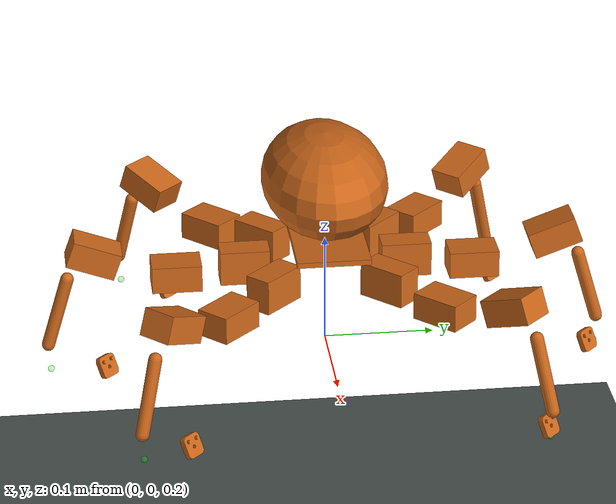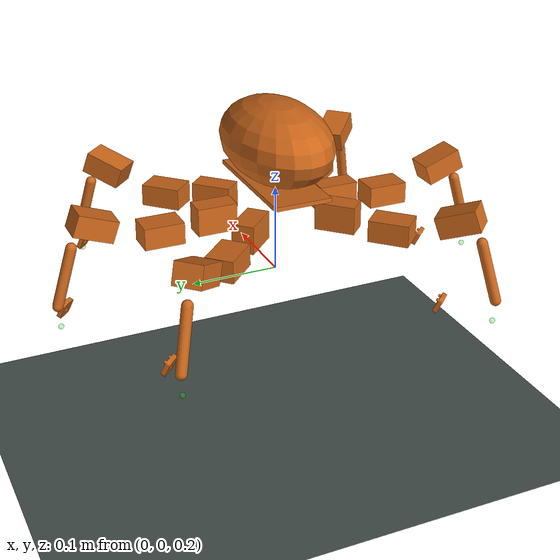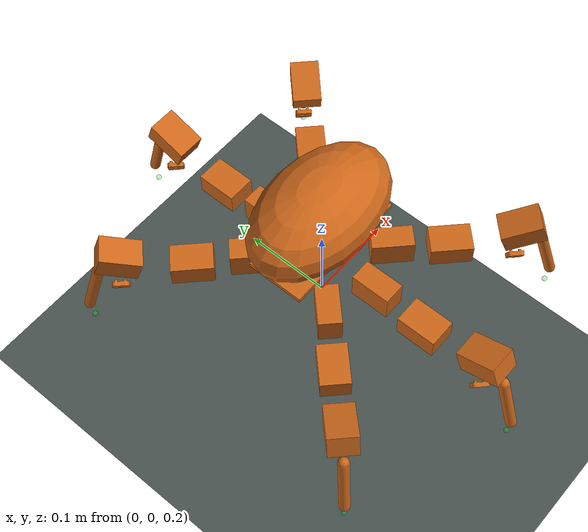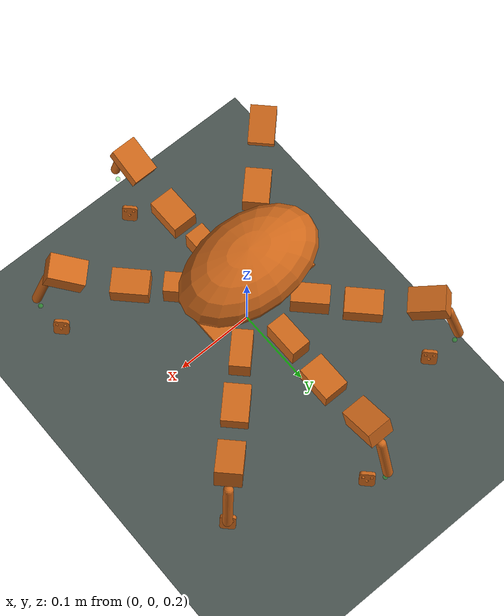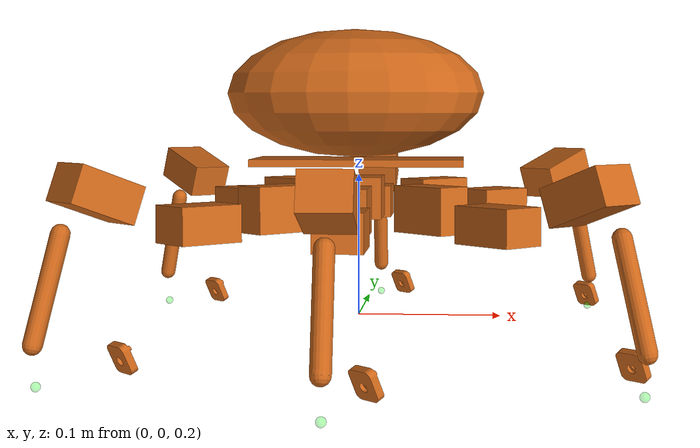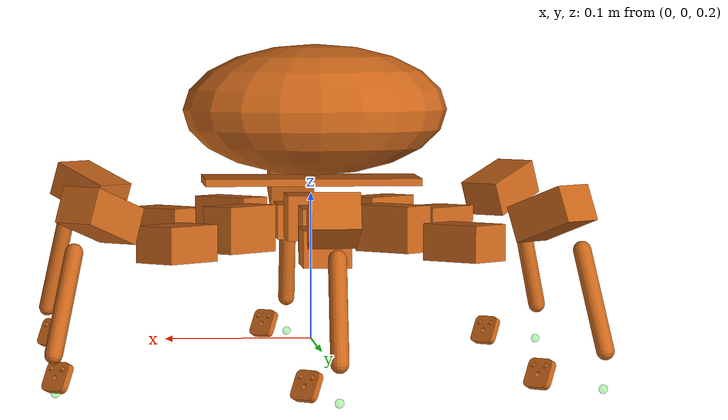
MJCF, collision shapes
<?xml version='1.0' encoding='utf-8'?>
<mujoco model="ARACHNE_18_V4_STS3215_12V_approx">
  <compiler angle="radian" autolimits="true" inertiafromgeom="false" meshdir="meshes" />
  <option timestep=".001" integrator="implicitfast" solver="Newton" iterations="60" cone="elliptic" />
  <visual>
    <global offwidth="1400" offheight="1000" azimuth="135" elevation="-25" />
  </visual>
  <asset>
    <texture name="floor_texture" type="2d" builtin="checker" rgb1="0.24 0.28 0.27" rgb2="0.32 0.36 0.34" width="512" height="512" />
    <material name="floor_mat" texture="floor_texture" texrepeat="8 8" reflectance="0.15" />
    <mesh name="01_CHASSIS" file="01_CHASSIS.stl" />
    <mesh name="02_CONTROLLER_CARRIER" file="02_CONTROLLER_CARRIER.stl" />
    <mesh name="05_SHELL" file="05_SHELL.stl" />
    <mesh name="REF_3S_BATTERY_115x40x35" file="REF_3S_BATTERY_115x40x35.stl" />
    <mesh name="REF_CONTROLLER_PCB_90x60" file="REF_CONTROLLER_PCB_90x60.stl" />
    <mesh name="REF_CONTROLLER_COMPONENTS" file="REF_CONTROLLER_COMPONENTS.stl" />
    <mesh name="BODY_carrier_insert_-64_-25" file="BODY_carrier_insert_-64_-25.stl" />
    <mesh name="BODY_carrier_M3x10_-64_-25" file="BODY_carrier_M3x10_-64_-25.stl" />
    <mesh name="BODY_carrier_insert_-64_25" file="BODY_carrier_insert_-64_25.stl" />
    <mesh name="BODY_carrier_M3x10_-64_25" file="BODY_carrier_M3x10_-64_25.stl" />
    <mesh name="BODY_carrier_insert_64_-25" file="BODY_carrier_insert_64_-25.stl" />
    <mesh name="BODY_carrier_M3x10_64_-25" file="BODY_carrier_M3x10_64_-25.stl" />
    <mesh name="BODY_carrier_insert_64_25" file="BODY_carrier_insert_64_25.stl" />
    <mesh name="BODY_carrier_M3x10_64_25" file="BODY_carrier_M3x10_64_25.stl" />
    <mesh name="BODY_cover_insert_-68_0" file="BODY_cover_insert_-68_0.stl" />
    <mesh name="BODY_cover_M3x10_-68_0" file="BODY_cover_M3x10_-68_0.stl" />
    <mesh name="BODY_cover_insert_68_0" file="BODY_cover_insert_68_0.stl" />
    <mesh name="BODY_cover_M3x10_68_0" file="BODY_cover_M3x10_68_0.stl" />
    <mesh name="BODY_PCB_standoff_-32_-24" file="BODY_PCB_standoff_-32_-24.stl" />
    <mesh name="BODY_PCB_insert_-32_-24" file="BODY_PCB_insert_-32_-24.stl" />
    <mesh name="BODY_PCB_M3x12_-32_-24" file="BODY_PCB_M3x12_-32_-24.stl" />
    <mesh name="BODY_PCB_standoff_-32_24" file="BODY_PCB_standoff_-32_24.stl" />
    <mesh name="BODY_PCB_insert_-32_24" file="BODY_PCB_insert_-32_24.stl" />
    <mesh name="BODY_PCB_M3x12_-32_24" file="BODY_PCB_M3x12_-32_24.stl" />
    <mesh name="BODY_PCB_standoff_32_-24" file="BODY_PCB_standoff_32_-24.stl" />
    <mesh name="BODY_PCB_insert_32_-24" file="BODY_PCB_insert_32_-24.stl" />
    <mesh name="BODY_PCB_M3x12_32_-24" file="BODY_PCB_M3x12_32_-24.stl" />
    <mesh name="BODY_PCB_standoff_32_24" file="BODY_PCB_standoff_32_24.stl" />
    <mesh name="BODY_PCB_insert_32_24" file="BODY_PCB_insert_32_24.stl" />
    <mesh name="BODY_PCB_M3x12_32_24" file="BODY_PCB_M3x12_32_24.stl" />
    <mesh name="L1_coxa" file="L1_coxa.stl" />
    <mesh name="L1_femur" file="L1_femur.stl" />
    <mesh name="L1_tibia" file="L1_tibia.stl" />
    <mesh name="L1_foot" file="L1_foot.stl" />
    <mesh name="L1_YAW_STS3215" file="L1_YAW_STS3215.stl" />
    <mesh name="L1_HIP_STS3215" file="L1_HIP_STS3215.stl" />
    <mesh name="L1_KNEE_STS3215" file="L1_KNEE_STS3215.stl" />
    <mesh name="L1_yaw_horn_-1" file="L1_yaw_horn_-1.stl" />
    <mesh name="L1_yaw_M3x6_-1_1" file="L1_yaw_M3x6_-1_1.stl" />
    <mesh name="L1_yaw_M3x6_-1_2" file="L1_yaw_M3x6_-1_2.stl" />
    <mesh name="L1_yaw_M3x6_-1_3" file="L1_yaw_M3x6_-1_3.stl" />
    <mesh name="L1_yaw_M3x6_-1_4" file="L1_yaw_M3x6_-1_4.stl" />
    <mesh name="L1_yaw_horn_1" file="L1_yaw_horn_1.stl" />
    <mesh name="L1_yaw_M3x6_1_1" file="L1_yaw_M3x6_1_1.stl" />
    <mesh name="L1_yaw_M3x6_1_2" file="L1_yaw_M3x6_1_2.stl" />
    <mesh name="L1_yaw_M3x6_1_3" file="L1_yaw_M3x6_1_3.stl" />
    <mesh name="L1_yaw_M3x6_1_4" file="L1_yaw_M3x6_1_4.stl" />
    <mesh name="L1_hip_horn_-1" file="L1_hip_horn_-1.stl" />
    <mesh name="L1_hip_M3x6_-1_1" file="L1_hip_M3x6_-1_1.stl" />
    <mesh name="L1_hip_M3x6_-1_2" file="L1_hip_M3x6_-1_2.stl" />
    <mesh name="L1_hip_M3x6_-1_3" file="L1_hip_M3x6_-1_3.stl" />
    <mesh name="L1_hip_M3x6_-1_4" file="L1_hip_M3x6_-1_4.stl" />
    <mesh name="L1_hip_horn_1" file="L1_hip_horn_1.stl" />
    <mesh name="L1_hip_M3x6_1_1" file="L1_hip_M3x6_1_1.stl" />
    <mesh name="L1_hip_M3x6_1_2" file="L1_hip_M3x6_1_2.stl" />
    <mesh name="L1_hip_M3x6_1_3" file="L1_hip_M3x6_1_3.stl" />
    <mesh name="L1_hip_M3x6_1_4" file="L1_hip_M3x6_1_4.stl" />
    <mesh name="L1_knee_horn_-1" file="L1_knee_horn_-1.stl" />
    <mesh name="L1_knee_M3x6_-1_1" file="L1_knee_M3x6_-1_1.stl" />
    <mesh name="L1_knee_M3x6_-1_2" file="L1_knee_M3x6_-1_2.stl" />
    <mesh name="L1_knee_M3x6_-1_3" file="L1_knee_M3x6_-1_3.stl" />
    <mesh name="L1_knee_M3x6_-1_4" file="L1_knee_M3x6_-1_4.stl" />
    <mesh name="L1_knee_horn_1" file="L1_knee_horn_1.stl" />
    <mesh name="L1_knee_M3x6_1_1" file="L1_knee_M3x6_1_1.stl" />
    <mesh name="L1_knee_M3x6_1_2" file="L1_knee_M3x6_1_2.stl" />
    <mesh name="L1_knee_M3x6_1_3" file="L1_knee_M3x6_1_3.stl" />
    <mesh name="L1_knee_M3x6_1_4" file="L1_knee_M3x6_1_4.stl" />
    <mesh name="L1_yaw_factory_PA2_-29_-10.25" file="L1_yaw_factory_PA2_-29_-10.25.stl" />
    <mesh name="L1_yaw_factory_PA2_-29_10.25" file="L1_yaw_factory_PA2_-29_10.25.stl" />
    <mesh name="L1_yaw_factory_PA2_-8.3_-10.25" file="L1_yaw_factory_PA2_-8.3_-10.25.stl" />
    <mesh name="L1_yaw_factory_PA2_-8.3_10.25" file="L1_yaw_factory_PA2_-8.3_10.25.stl" />
    <mesh name="L1_hip_factory_PA2_-29_-10.25" file="L1_hip_factory_PA2_-29_-10.25.stl" />
    <mesh name="L1_hip_factory_PA2_-29_10.25" file="L1_hip_factory_PA2_-29_10.25.stl" />
    <mesh name="L1_hip_factory_PA2_-8.3_-10.25" file="L1_hip_factory_PA2_-8.3_-10.25.stl" />
    <mesh name="L1_hip_factory_PA2_-8.3_10.25" file="L1_hip_factory_PA2_-8.3_10.25.stl" />
    <mesh name="L1_knee_factory_PA2_-29_-10.25" file="L1_knee_factory_PA2_-29_-10.25.stl" />
    <mesh name="L1_knee_factory_PA2_-29_10.25" file="L1_knee_factory_PA2_-29_10.25.stl" />
    <mesh name="L1_knee_factory_PA2_-8.3_-10.25" file="L1_knee_factory_PA2_-8.3_-10.25.stl" />
    <mesh name="L1_knee_factory_PA2_-8.3_10.25" file="L1_knee_factory_PA2_-8.3_10.25.stl" />
    <mesh name="L1_shoe_insert" file="L1_shoe_insert.stl" />
    <mesh name="L1_shoe_M3x8" file="L1_shoe_M3x8.stl" />
    <mesh name="L2_coxa" file="L2_coxa.stl" />
    <mesh name="L2_femur" file="L2_femur.stl" />
    <mesh name="L2_tibia" file="L2_tibia.stl" />
    <mesh name="L2_foot" file="L2_foot.stl" />
    <mesh name="L2_YAW_STS3215" file="L2_YAW_STS3215.stl" />
    <mesh name="L2_HIP_STS3215" file="L2_HIP_STS3215.stl" />
    <mesh name="L2_KNEE_STS3215" file="L2_KNEE_STS3215.stl" />
    <mesh name="L2_yaw_horn_-1" file="L2_yaw_horn_-1.stl" />
    <mesh name="L2_yaw_M3x6_-1_1" file="L2_yaw_M3x6_-1_1.stl" />
    <mesh name="L2_yaw_M3x6_-1_2" file="L2_yaw_M3x6_-1_2.stl" />
    <mesh name="L2_yaw_M3x6_-1_3" file="L2_yaw_M3x6_-1_3.stl" />
    <mesh name="L2_yaw_M3x6_-1_4" file="L2_yaw_M3x6_-1_4.stl" />
    <mesh name="L2_yaw_horn_1" file="L2_yaw_horn_1.stl" />
    <mesh name="L2_yaw_M3x6_1_1" file="L2_yaw_M3x6_1_1.stl" />
    <mesh name="L2_yaw_M3x6_1_2" file="L2_yaw_M3x6_1_2.stl" />
    <mesh name="L2_yaw_M3x6_1_3" file="L2_yaw_M3x6_1_3.stl" />
    <mesh name="L2_yaw_M3x6_1_4" file="L2_yaw_M3x6_1_4.stl" />
    <mesh name="L2_hip_horn_-1" file="L2_hip_horn_-1.stl" />
    <mesh name="L2_hip_M3x6_-1_1" file="L2_hip_M3x6_-1_1.stl" />
    <mesh name="L2_hip_M3x6_-1_2" file="L2_hip_M3x6_-1_2.stl" />
    <mesh name="L2_hip_M3x6_-1_3" file="L2_hip_M3x6_-1_3.stl" />
    <mesh name="L2_hip_M3x6_-1_4" file="L2_hip_M3x6_-1_4.stl" />
    <mesh name="L2_hip_horn_1" file="L2_hip_horn_1.stl" />
    <mesh name="L2_hip_M3x6_1_1" file="L2_hip_M3x6_1_1.stl" />
    <mesh name="L2_hip_M3x6_1_2" file="L2_hip_M3x6_1_2.stl" />
    <mesh name="L2_hip_M3x6_1_3" file="L2_hip_M3x6_1_3.stl" />
    <mesh name="L2_hip_M3x6_1_4" file="L2_hip_M3x6_1_4.stl" />
    <mesh name="L2_knee_horn_-1" file="L2_knee_horn_-1.stl" />
    <mesh name="L2_knee_M3x6_-1_1" file="L2_knee_M3x6_-1_1.stl" />
    <mesh name="L2_knee_M3x6_-1_2" file="L2_knee_M3x6_-1_2.stl" />
    <mesh name="L2_knee_M3x6_-1_3" file="L2_knee_M3x6_-1_3.stl" />
    <mesh name="L2_knee_M3x6_-1_4" file="L2_knee_M3x6_-1_4.stl" />
    <mesh name="L2_knee_horn_1" file="L2_knee_horn_1.stl" />
    <mesh name="L2_knee_M3x6_1_1" file="L2_knee_M3x6_1_1.stl" />
    <mesh name="L2_knee_M3x6_1_2" file="L2_knee_M3x6_1_2.stl" />
    <mesh name="L2_knee_M3x6_1_3" file="L2_knee_M3x6_1_3.stl" />
    <mesh name="L2_knee_M3x6_1_4" file="L2_knee_M3x6_1_4.stl" />
    <mesh name="L2_yaw_factory_PA2_-29_-10.25" file="L2_yaw_factory_PA2_-29_-10.25.stl" />
    <mesh name="L2_yaw_factory_PA2_-29_10.25" file="L2_yaw_factory_PA2_-29_10.25.stl" />
    <mesh name="L2_yaw_factory_PA2_-8.3_-10.25" file="L2_yaw_factory_PA2_-8.3_-10.25.stl" />
    <mesh name="L2_yaw_factory_PA2_-8.3_10.25" file="L2_yaw_factory_PA2_-8.3_10.25.stl" />
    <mesh name="L2_hip_factory_PA2_-29_-10.25" file="L2_hip_factory_PA2_-29_-10.25.stl" />
    <mesh name="L2_hip_factory_PA2_-29_10.25" file="L2_hip_factory_PA2_-29_10.25.stl" />
    <mesh name="L2_hip_factory_PA2_-8.3_-10.25" file="L2_hip_factory_PA2_-8.3_-10.25.stl" />
    <mesh name="L2_hip_factory_PA2_-8.3_10.25" file="L2_hip_factory_PA2_-8.3_10.25.stl" />
    <mesh name="L2_knee_factory_PA2_-29_-10.25" file="L2_knee_factory_PA2_-29_-10.25.stl" />
    <mesh name="L2_knee_factory_PA2_-29_10.25" file="L2_knee_factory_PA2_-29_10.25.stl" />
    <mesh name="L2_knee_factory_PA2_-8.3_-10.25" file="L2_knee_factory_PA2_-8.3_-10.25.stl" />
    <mesh name="L2_knee_factory_PA2_-8.3_10.25" file="L2_knee_factory_PA2_-8.3_10.25.stl" />
    <mesh name="L2_shoe_insert" file="L2_shoe_insert.stl" />
    <mesh name="L2_shoe_M3x8" file="L2_shoe_M3x8.stl" />
    <mesh name="L3_coxa" file="L3_coxa.stl" />
    <mesh name="L3_femur" file="L3_femur.stl" />
    <mesh name="L3_tibia" file="L3_tibia.stl" />
    <mesh name="L3_foot" file="L3_foot.stl" />
    <mesh name="L3_YAW_STS3215" file="L3_YAW_STS3215.stl" />
    <mesh name="L3_HIP_STS3215" file="L3_HIP_STS3215.stl" />
    <mesh name="L3_KNEE_STS3215" file="L3_KNEE_STS3215.stl" />
    <mesh name="L3_yaw_horn_-1" file="L3_yaw_horn_-1.stl" />
    <mesh name="L3_yaw_M3x6_-1_1" file="L3_yaw_M3x6_-1_1.stl" />
    <mesh name="L3_yaw_M3x6_-1_2" file="L3_yaw_M3x6_-1_2.stl" />
    <mesh name="L3_yaw_M3x6_-1_3" file="L3_yaw_M3x6_-1_3.stl" />
    <mesh name="L3_yaw_M3x6_-1_4" file="L3_yaw_M3x6_-1_4.stl" />
    <mesh name="L3_yaw_horn_1" file="L3_yaw_horn_1.stl" />
    <mesh name="L3_yaw_M3x6_1_1" file="L3_yaw_M3x6_1_1.stl" />
    <mesh name="L3_yaw_M3x6_1_2" file="L3_yaw_M3x6_1_2.stl" />
    <mesh name="L3_yaw_M3x6_1_3" file="L3_yaw_M3x6_1_3.stl" />
    <mesh name="L3_yaw_M3x6_1_4" file="L3_yaw_M3x6_1_4.stl" />
    <mesh name="L3_hip_horn_-1" file="L3_hip_horn_-1.stl" />
    <mesh name="L3_hip_M3x6_-1_1" file="L3_hip_M3x6_-1_1.stl" />
    <mesh name="L3_hip_M3x6_-1_2" file="L3_hip_M3x6_-1_2.stl" />
    <mesh name="L3_hip_M3x6_-1_3" file="L3_hip_M3x6_-1_3.stl" />
    <mesh name="L3_hip_M3x6_-1_4" file="L3_hip_M3x6_-1_4.stl" />
    <mesh name="L3_hip_horn_1" file="L3_hip_horn_1.stl" />
    <mesh name="L3_hip_M3x6_1_1" file="L3_hip_M3x6_1_1.stl" />
    <mesh name="L3_hip_M3x6_1_2" file="L3_hip_M3x6_1_2.stl" />
    <mesh name="L3_hip_M3x6_1_3" file="L3_hip_M3x6_1_3.stl" />
    <mesh name="L3_hip_M3x6_1_4" file="L3_hip_M3x6_1_4.stl" />
    <mesh name="L3_knee_horn_-1" file="L3_knee_horn_-1.stl" />
    <mesh name="L3_knee_M3x6_-1_1" file="L3_knee_M3x6_-1_1.stl" />
    <mesh name="L3_knee_M3x6_-1_2" file="L3_knee_M3x6_-1_2.stl" />
    <mesh name="L3_knee_M3x6_-1_3" file="L3_knee_M3x6_-1_3.stl" />
    <mesh name="L3_knee_M3x6_-1_4" file="L3_knee_M3x6_-1_4.stl" />
    <mesh name="L3_knee_horn_1" file="L3_knee_horn_1.stl" />
    <mesh name="L3_knee_M3x6_1_1" file="L3_knee_M3x6_1_1.stl" />
    <mesh name="L3_knee_M3x6_1_2" file="L3_knee_M3x6_1_2.stl" />
    <mesh name="L3_knee_M3x6_1_3" file="L3_knee_M3x6_1_3.stl" />
    <mesh name="L3_knee_M3x6_1_4" file="L3_knee_M3x6_1_4.stl" />
    <mesh name="L3_yaw_factory_PA2_-29_-10.25" file="L3_yaw_factory_PA2_-29_-10.25.stl" />
    <mesh name="L3_yaw_factory_PA2_-29_10.25" file="L3_yaw_factory_PA2_-29_10.25.stl" />
    <mesh name="L3_yaw_factory_PA2_-8.3_-10.25" file="L3_yaw_factory_PA2_-8.3_-10.25.stl" />
    <mesh name="L3_yaw_factory_PA2_-8.3_10.25" file="L3_yaw_factory_PA2_-8.3_10.25.stl" />
    <mesh name="L3_hip_factory_PA2_-29_-10.25" file="L3_hip_factory_PA2_-29_-10.25.stl" />
    <mesh name="L3_hip_factory_PA2_-29_10.25" file="L3_hip_factory_PA2_-29_10.25.stl" />
    <mesh name="L3_hip_factory_PA2_-8.3_-10.25" file="L3_hip_factory_PA2_-8.3_-10.25.stl" />
    <mesh name="L3_hip_factory_PA2_-8.3_10.25" file="L3_hip_factory_PA2_-8.3_10.25.stl" />
    <mesh name="L3_knee_factory_PA2_-29_-10.25" file="L3_knee_factory_PA2_-29_-10.25.stl" />
    <mesh name="L3_knee_factory_PA2_-29_10.25" file="L3_knee_factory_PA2_-29_10.25.stl" />
    <mesh name="L3_knee_factory_PA2_-8.3_-10.25" file="L3_knee_factory_PA2_-8.3_-10.25.stl" />
    <mesh name="L3_knee_factory_PA2_-8.3_10.25" file="L3_knee_factory_PA2_-8.3_10.25.stl" />
    <mesh name="L3_shoe_insert" file="L3_shoe_insert.stl" />
    <mesh name="L3_shoe_M3x8" file="L3_shoe_M3x8.stl" />
    <mesh name="L4_coxa" file="L4_coxa.stl" />
    <mesh name="L4_femur" file="L4_femur.stl" />
    <mesh name="L4_tibia" file="L4_tibia.stl" />
    <mesh name="L4_foot" file="L4_foot.stl" />
    <mesh name="L4_YAW_STS3215" file="L4_YAW_STS3215.stl" />
    <mesh name="L4_HIP_STS3215" file="L4_HIP_STS3215.stl" />
    <mesh name="L4_KNEE_STS3215" file="L4_KNEE_STS3215.stl" />
    <mesh name="L4_yaw_horn_-1" file="L4_yaw_horn_-1.stl" />
    <mesh name="L4_yaw_M3x6_-1_1" file="L4_yaw_M3x6_-1_1.stl" />
    <mesh name="L4_yaw_M3x6_-1_2" file="L4_yaw_M3x6_-1_2.stl" />
    <mesh name="L4_yaw_M3x6_-1_3" file="L4_yaw_M3x6_-1_3.stl" />
    <mesh name="L4_yaw_M3x6_-1_4" file="L4_yaw_M3x6_-1_4.stl" />
    <mesh name="L4_yaw_horn_1" file="L4_yaw_horn_1.stl" />
    <mesh name="L4_yaw_M3x6_1_1" file="L4_yaw_M3x6_1_1.stl" />
    <mesh name="L4_yaw_M3x6_1_2" file="L4_yaw_M3x6_1_2.stl" />
    <mesh name="L4_yaw_M3x6_1_3" file="L4_yaw_M3x6_1_3.stl" />
    <mesh name="L4_yaw_M3x6_1_4" file="L4_yaw_M3x6_1_4.stl" />
    <mesh name="L4_hip_horn_-1" file="L4_hip_horn_-1.stl" />
    <mesh name="L4_hip_M3x6_-1_1" file="L4_hip_M3x6_-1_1.stl" />
    <mesh name="L4_hip_M3x6_-1_2" file="L4_hip_M3x6_-1_2.stl" />
    <mesh name="L4_hip_M3x6_-1_3" file="L4_hip_M3x6_-1_3.stl" />
    <mesh name="L4_hip_M3x6_-1_4" file="L4_hip_M3x6_-1_4.stl" />
    <mesh name="L4_hip_horn_1" file="L4_hip_horn_1.stl" />
    <mesh name="L4_hip_M3x6_1_1" file="L4_hip_M3x6_1_1.stl" />
    <mesh name="L4_hip_M3x6_1_2" file="L4_hip_M3x6_1_2.stl" />
    <mesh name="L4_hip_M3x6_1_3" file="L4_hip_M3x6_1_3.stl" />
    <mesh name="L4_hip_M3x6_1_4" file="L4_hip_M3x6_1_4.stl" />
    <mesh name="L4_knee_horn_-1" file="L4_knee_horn_-1.stl" />
    <mesh name="L4_knee_M3x6_-1_1" file="L4_knee_M3x6_-1_1.stl" />
    <mesh name="L4_knee_M3x6_-1_2" file="L4_knee_M3x6_-1_2.stl" />
    <mesh name="L4_knee_M3x6_-1_3" file="L4_knee_M3x6_-1_3.stl" />
    <mesh name="L4_knee_M3x6_-1_4" file="L4_knee_M3x6_-1_4.stl" />
    <mesh name="L4_knee_horn_1" file="L4_knee_horn_1.stl" />
    <mesh name="L4_knee_M3x6_1_1" file="L4_knee_M3x6_1_1.stl" />
    <mesh name="L4_knee_M3x6_1_2" file="L4_knee_M3x6_1_2.stl" />
    <mesh name="L4_knee_M3x6_1_3" file="L4_knee_M3x6_1_3.stl" />
    <mesh name="L4_knee_M3x6_1_4" file="L4_knee_M3x6_1_4.stl" />
    <mesh name="L4_yaw_factory_PA2_-29_-10.25" file="L4_yaw_factory_PA2_-29_-10.25.stl" />
    <mesh name="L4_yaw_factory_PA2_-29_10.25" file="L4_yaw_factory_PA2_-29_10.25.stl" />
    <mesh name="L4_yaw_factory_PA2_-8.3_-10.25" file="L4_yaw_factory_PA2_-8.3_-10.25.stl" />
    <mesh name="L4_yaw_factory_PA2_-8.3_10.25" file="L4_yaw_factory_PA2_-8.3_10.25.stl" />
    <mesh name="L4_hip_factory_PA2_-29_-10.25" file="L4_hip_factory_PA2_-29_-10.25.stl" />
    <mesh name="L4_hip_factory_PA2_-29_10.25" file="L4_hip_factory_PA2_-29_10.25.stl" />
    <mesh name="L4_hip_factory_PA2_-8.3_-10.25" file="L4_hip_factory_PA2_-8.3_-10.25.stl" />
    <mesh name="L4_hip_factory_PA2_-8.3_10.25" file="L4_hip_factory_PA2_-8.3_10.25.stl" />
    <mesh name="L4_knee_factory_PA2_-29_-10.25" file="L4_knee_factory_PA2_-29_-10.25.stl" />
    <mesh name="L4_knee_factory_PA2_-29_10.25" file="L4_knee_factory_PA2_-29_10.25.stl" />
    <mesh name="L4_knee_factory_PA2_-8.3_-10.25" file="L4_knee_factory_PA2_-8.3_-10.25.stl" />
    <mesh name="L4_knee_factory_PA2_-8.3_10.25" file="L4_knee_factory_PA2_-8.3_10.25.stl" />
    <mesh name="L4_shoe_insert" file="L4_shoe_insert.stl" />
    <mesh name="L4_shoe_M3x8" file="L4_shoe_M3x8.stl" />
    <mesh name="L5_coxa" file="L5_coxa.stl" />
    <mesh name="L5_femur" file="L5_femur.stl" />
    <mesh name="L5_tibia" file="L5_tibia.stl" />
    <mesh name="L5_foot" file="L5_foot.stl" />
    <mesh name="L5_YAW_STS3215" file="L5_YAW_STS3215.stl" />
    <mesh name="L5_HIP_STS3215" file="L5_HIP_STS3215.stl" />
    <mesh name="L5_KNEE_STS3215" file="L5_KNEE_STS3215.stl" />
    <mesh name="L5_yaw_horn_-1" file="L5_yaw_horn_-1.stl" />
    <mesh name="L5_yaw_M3x6_-1_1" file="L5_yaw_M3x6_-1_1.stl" />
    <mesh name="L5_yaw_M3x6_-1_2" file="L5_yaw_M3x6_-1_2.stl" />
    <mesh name="L5_yaw_M3x6_-1_3" file="L5_yaw_M3x6_-1_3.stl" />
    <mesh name="L5_yaw_M3x6_-1_4" file="L5_yaw_M3x6_-1_4.stl" />
    <mesh name="L5_yaw_horn_1" file="L5_yaw_horn_1.stl" />
    <mesh name="L5_yaw_M3x6_1_1" file="L5_yaw_M3x6_1_1.stl" />
    <mesh name="L5_yaw_M3x6_1_2" file="L5_yaw_M3x6_1_2.stl" />
    <mesh name="L5_yaw_M3x6_1_3" file="L5_yaw_M3x6_1_3.stl" />
    <mesh name="L5_yaw_M3x6_1_4" file="L5_yaw_M3x6_1_4.stl" />
    <mesh name="L5_hip_horn_-1" file="L5_hip_horn_-1.stl" />
    <mesh name="L5_hip_M3x6_-1_1" file="L5_hip_M3x6_-1_1.stl" />
    <mesh name="L5_hip_M3x6_-1_2" file="L5_hip_M3x6_-1_2.stl" />
    <mesh name="L5_hip_M3x6_-1_3" file="L5_hip_M3x6_-1_3.stl" />
    <mesh name="L5_hip_M3x6_-1_4" file="L5_hip_M3x6_-1_4.stl" />
    <mesh name="L5_hip_horn_1" file="L5_hip_horn_1.stl" />
    <mesh name="L5_hip_M3x6_1_1" file="L5_hip_M3x6_1_1.stl" />
    <mesh name="L5_hip_M3x6_1_2" file="L5_hip_M3x6_1_2.stl" />
    <mesh name="L5_hip_M3x6_1_3" file="L5_hip_M3x6_1_3.stl" />
    <mesh name="L5_hip_M3x6_1_4" file="L5_hip_M3x6_1_4.stl" />
    <mesh name="L5_knee_horn_-1" file="L5_knee_horn_-1.stl" />
    <mesh name="L5_knee_M3x6_-1_1" file="L5_knee_M3x6_-1_1.stl" />
    <mesh name="L5_knee_M3x6_-1_2" file="L5_knee_M3x6_-1_2.stl" />
    <mesh name="L5_knee_M3x6_-1_3" file="L5_knee_M3x6_-1_3.stl" />
    <mesh name="L5_knee_M3x6_-1_4" file="L5_knee_M3x6_-1_4.stl" />
    <mesh name="L5_knee_horn_1" file="L5_knee_horn_1.stl" />
    <mesh name="L5_knee_M3x6_1_1" file="L5_knee_M3x6_1_1.stl" />
    <mesh name="L5_knee_M3x6_1_2" file="L5_knee_M3x6_1_2.stl" />
    <mesh name="L5_knee_M3x6_1_3" file="L5_knee_M3x6_1_3.stl" />
    <mesh name="L5_knee_M3x6_1_4" file="L5_knee_M3x6_1_4.stl" />
    <mesh name="L5_yaw_factory_PA2_-29_-10.25" file="L5_yaw_factory_PA2_-29_-10.25.stl" />
    <mesh name="L5_yaw_factory_PA2_-29_10.25" file="L5_yaw_factory_PA2_-29_10.25.stl" />
    <mesh name="L5_yaw_factory_PA2_-8.3_-10.25" file="L5_yaw_factory_PA2_-8.3_-10.25.stl" />
    <mesh name="L5_yaw_factory_PA2_-8.3_10.25" file="L5_yaw_factory_PA2_-8.3_10.25.stl" />
    <mesh name="L5_hip_factory_PA2_-29_-10.25" file="L5_hip_factory_PA2_-29_-10.25.stl" />
    <mesh name="L5_hip_factory_PA2_-29_10.25" file="L5_hip_factory_PA2_-29_10.25.stl" />
    <mesh name="L5_hip_factory_PA2_-8.3_-10.25" file="L5_hip_factory_PA2_-8.3_-10.25.stl" />
    <mesh name="L5_hip_factory_PA2_-8.3_10.25" file="L5_hip_factory_PA2_-8.3_10.25.stl" />
    <mesh name="L5_knee_factory_PA2_-29_-10.25" file="L5_knee_factory_PA2_-29_-10.25.stl" />
    <mesh name="L5_knee_factory_PA2_-29_10.25" file="L5_knee_factory_PA2_-29_10.25.stl" />
    <mesh name="L5_knee_factory_PA2_-8.3_-10.25" file="L5_knee_factory_PA2_-8.3_-10.25.stl" />
    <mesh name="L5_knee_factory_PA2_-8.3_10.25" file="L5_knee_factory_PA2_-8.3_10.25.stl" />
    <mesh name="L5_shoe_insert" file="L5_shoe_insert.stl" />
    <mesh name="L5_shoe_M3x8" file="L5_shoe_M3x8.stl" />
    <mesh name="L6_coxa" file="L6_coxa.stl" />
    <mesh name="L6_femur" file="L6_femur.stl" />
    <mesh name="L6_tibia" file="L6_tibia.stl" />
    <mesh name="L6_foot" file="L6_foot.stl" />
    <mesh name="L6_YAW_STS3215" file="L6_YAW_STS3215.stl" />
    <mesh name="L6_HIP_STS3215" file="L6_HIP_STS3215.stl" />
    <mesh name="L6_KNEE_STS3215" file="L6_KNEE_STS3215.stl" />
    <mesh name="L6_yaw_horn_-1" file="L6_yaw_horn_-1.stl" />
    <mesh name="L6_yaw_M3x6_-1_1" file="L6_yaw_M3x6_-1_1.stl" />
    <mesh name="L6_yaw_M3x6_-1_2" file="L6_yaw_M3x6_-1_2.stl" />
    <mesh name="L6_yaw_M3x6_-1_3" file="L6_yaw_M3x6_-1_3.stl" />
    <mesh name="L6_yaw_M3x6_-1_4" file="L6_yaw_M3x6_-1_4.stl" />
    <mesh name="L6_yaw_horn_1" file="L6_yaw_horn_1.stl" />
    <mesh name="L6_yaw_M3x6_1_1" file="L6_yaw_M3x6_1_1.stl" />
    <mesh name="L6_yaw_M3x6_1_2" file="L6_yaw_M3x6_1_2.stl" />
    <mesh name="L6_yaw_M3x6_1_3" file="L6_yaw_M3x6_1_3.stl" />
    <mesh name="L6_yaw_M3x6_1_4" file="L6_yaw_M3x6_1_4.stl" />
    <mesh name="L6_hip_horn_-1" file="L6_hip_horn_-1.stl" />
    <mesh name="L6_hip_M3x6_-1_1" file="L6_hip_M3x6_-1_1.stl" />
    <mesh name="L6_hip_M3x6_-1_2" file="L6_hip_M3x6_-1_2.stl" />
    <mesh name="L6_hip_M3x6_-1_3" file="L6_hip_M3x6_-1_3.stl" />
    <mesh name="L6_hip_M3x6_-1_4" file="L6_hip_M3x6_-1_4.stl" />
    <mesh name="L6_hip_horn_1" file="L6_hip_horn_1.stl" />
    <mesh name="L6_hip_M3x6_1_1" file="L6_hip_M3x6_1_1.stl" />
    <mesh name="L6_hip_M3x6_1_2" file="L6_hip_M3x6_1_2.stl" />
    <mesh name="L6_hip_M3x6_1_3" file="L6_hip_M3x6_1_3.stl" />
    <mesh name="L6_hip_M3x6_1_4" file="L6_hip_M3x6_1_4.stl" />
    <mesh name="L6_knee_horn_-1" file="L6_knee_horn_-1.stl" />
    <mesh name="L6_knee_M3x6_-1_1" file="L6_knee_M3x6_-1_1.stl" />
    <mesh name="L6_knee_M3x6_-1_2" file="L6_knee_M3x6_-1_2.stl" />
    <mesh name="L6_knee_M3x6_-1_3" file="L6_knee_M3x6_-1_3.stl" />
    <mesh name="L6_knee_M3x6_-1_4" file="L6_knee_M3x6_-1_4.stl" />
    <mesh name="L6_knee_horn_1" file="L6_knee_horn_1.stl" />
    <mesh name="L6_knee_M3x6_1_1" file="L6_knee_M3x6_1_1.stl" />
    <mesh name="L6_knee_M3x6_1_2" file="L6_knee_M3x6_1_2.stl" />
    <mesh name="L6_knee_M3x6_1_3" file="L6_knee_M3x6_1_3.stl" />
    <mesh name="L6_knee_M3x6_1_4" file="L6_knee_M3x6_1_4.stl" />
    <mesh name="L6_yaw_factory_PA2_-29_-10.25" file="L6_yaw_factory_PA2_-29_-10.25.stl" />
    <mesh name="L6_yaw_factory_PA2_-29_10.25" file="L6_yaw_factory_PA2_-29_10.25.stl" />
    <mesh name="L6_yaw_factory_PA2_-8.3_-10.25" file="L6_yaw_factory_PA2_-8.3_-10.25.stl" />
    <mesh name="L6_yaw_factory_PA2_-8.3_10.25" file="L6_yaw_factory_PA2_-8.3_10.25.stl" />
    <mesh name="L6_hip_factory_PA2_-29_-10.25" file="L6_hip_factory_PA2_-29_-10.25.stl" />
    <mesh name="L6_hip_factory_PA2_-29_10.25" file="L6_hip_factory_PA2_-29_10.25.stl" />
    <mesh name="L6_hip_factory_PA2_-8.3_-10.25" file="L6_hip_factory_PA2_-8.3_-10.25.stl" />
    <mesh name="L6_hip_factory_PA2_-8.3_10.25" file="L6_hip_factory_PA2_-8.3_10.25.stl" />
    <mesh name="L6_knee_factory_PA2_-29_-10.25" file="L6_knee_factory_PA2_-29_-10.25.stl" />
    <mesh name="L6_knee_factory_PA2_-29_10.25" file="L6_knee_factory_PA2_-29_10.25.stl" />
    <mesh name="L6_knee_factory_PA2_-8.3_-10.25" file="L6_knee_factory_PA2_-8.3_-10.25.stl" />
    <mesh name="L6_knee_factory_PA2_-8.3_10.25" file="L6_knee_factory_PA2_-8.3_10.25.stl" />
    <mesh name="L6_shoe_insert" file="L6_shoe_insert.stl" />
    <mesh name="L6_shoe_M3x8" file="L6_shoe_M3x8.stl" />
  </asset>
  <default>
    <joint limited="true" damping=".02" armature=".0001" frictionloss=".001" />
    <geom friction="0.8 0.005 0.0002" solref="0.006 1" solimp="0.95 0.99 0.001" condim="4" />
  </default>
  <worldbody>
    <light pos="0.2 -0.4 1.5" dir="-0.2 0.4 -1" diffuse="0.9 0.9 0.9" castshadow="true" />
    <geom name="ground" type="plane" size="2 2 0.1" material="floor_mat" />
    <body name="BODY" pos="0 0 0.2794269501">
      <site name="imu" size="0.004" pos="0 0 0.078" />
      <camera name="follow" mode="trackcom" pos="0.65 -0.85 0.5" xyaxes="0.794 0.607 0 -0.24 0.32 0.916" />
      <inertial pos="-0.0001359806082 -6.072240062e-08 0.03244114199" mass="0.9661702469287098" fullinertia="0.002853235441 0.002784673935 0.003409356017 3.206102527e-09 1.428502686e-05 4.968615479e-09" />
      <geom name="01_CHASSIS_visual" type="mesh" mesh="01_CHASSIS" rgba="0.13 0.46 0.44 1" contype="0" conaffinity="0" group="2" />
      <geom name="02_CONTROLLER_CARRIER_visual" type="mesh" mesh="02_CONTROLLER_CARRIER" rgba="0.13 0.46 0.44 1" contype="0" conaffinity="0" group="2" />
      <geom name="05_SHELL_visual" type="mesh" mesh="05_SHELL" rgba="0.13 0.46 0.44 1" contype="0" conaffinity="0" group="2" />
      <geom name="REF_3S_BATTERY_115x40x35_visual" type="mesh" mesh="REF_3S_BATTERY_115x40x35" rgba="0.65 0.42 0.12 1" contype="0" conaffinity="0" group="2" />
      <geom name="REF_CONTROLLER_PCB_90x60_visual" type="mesh" mesh="REF_CONTROLLER_PCB_90x60" rgba="0.13 0.34 0.2 1" contype="0" conaffinity="0" group="2" />
      <geom name="REF_CONTROLLER_COMPONENTS_visual" type="mesh" mesh="REF_CONTROLLER_COMPONENTS" rgba="0.19 0.21 0.25 1" contype="0" conaffinity="0" group="2" />
      <geom name="BODY_carrier_insert_-64_-25_visual" type="mesh" mesh="BODY_carrier_insert_-64_-25" rgba="0.73 0.52 0.19 1" contype="0" conaffinity="0" group="2" />
      <geom name="BODY_carrier_M3x10_-64_-25_visual" type="mesh" mesh="BODY_carrier_M3x10_-64_-25" rgba="0.68 0.71 0.74 1" contype="0" conaffinity="0" group="2" />
      <geom name="BODY_carrier_insert_-64_25_visual" type="mesh" mesh="BODY_carrier_insert_-64_25" rgba="0.73 0.52 0.19 1" contype="0" conaffinity="0" group="2" />
      <geom name="BODY_carrier_M3x10_-64_25_visual" type="mesh" mesh="BODY_carrier_M3x10_-64_25" rgba="0.68 0.71 0.74 1" contype="0" conaffinity="0" group="2" />
      <geom name="BODY_carrier_insert_64_-25_visual" type="mesh" mesh="BODY_carrier_insert_64_-25" rgba="0.73 0.52 0.19 1" contype="0" conaffinity="0" group="2" />
      <geom name="BODY_carrier_M3x10_64_-25_visual" type="mesh" mesh="BODY_carrier_M3x10_64_-25" rgba="0.68 0.71 0.74 1" contype="0" conaffinity="0" group="2" />
      <geom name="BODY_carrier_insert_64_25_visual" type="mesh" mesh="BODY_carrier_insert_64_25" rgba="0.73 0.52 0.19 1" contype="0" conaffinity="0" group="2" />
      <geom name="BODY_carrier_M3x10_64_25_visual" type="mesh" mesh="BODY_carrier_M3x10_64_25" rgba="0.68 0.71 0.74 1" contype="0" conaffinity="0" group="2" />
      <geom name="BODY_cover_insert_-68_0_visual" type="mesh" mesh="BODY_cover_insert_-68_0" rgba="0.73 0.52 0.19 1" contype="0" conaffinity="0" group="2" />
      <geom name="BODY_cover_M3x10_-68_0_visual" type="mesh" mesh="BODY_cover_M3x10_-68_0" rgba="0.68 0.71 0.74 1" contype="0" conaffinity="0" group="2" />
      <geom name="BODY_cover_insert_68_0_visual" type="mesh" mesh="BODY_cover_insert_68_0" rgba="0.73 0.52 0.19 1" contype="0" conaffinity="0" group="2" />
      <geom name="BODY_cover_M3x10_68_0_visual" type="mesh" mesh="BODY_cover_M3x10_68_0" rgba="0.68 0.71 0.74 1" contype="0" conaffinity="0" group="2" />
      <geom name="BODY_PCB_standoff_-32_-24_visual" type="mesh" mesh="BODY_PCB_standoff_-32_-24" rgba="0.13 0.46 0.44 1" contype="0" conaffinity="0" group="2" />
      <geom name="BODY_PCB_insert_-32_-24_visual" type="mesh" mesh="BODY_PCB_insert_-32_-24" rgba="0.73 0.52 0.19 1" contype="0" conaffinity="0" group="2" />
      <geom name="BODY_PCB_M3x12_-32_-24_visual" type="mesh" mesh="BODY_PCB_M3x12_-32_-24" rgba="0.68 0.71 0.74 1" contype="0" conaffinity="0" group="2" />
      <geom name="BODY_PCB_standoff_-32_24_visual" type="mesh" mesh="BODY_PCB_standoff_-32_24" rgba="0.13 0.46 0.44 1" contype="0" conaffinity="0" group="2" />
      <geom name="BODY_PCB_insert_-32_24_visual" type="mesh" mesh="BODY_PCB_insert_-32_24" rgba="0.73 0.52 0.19 1" contype="0" conaffinity="0" group="2" />
      <geom name="BODY_PCB_M3x12_-32_24_visual" type="mesh" mesh="BODY_PCB_M3x12_-32_24" rgba="0.68 0.71 0.74 1" contype="0" conaffinity="0" group="2" />
      <geom name="BODY_PCB_standoff_32_-24_visual" type="mesh" mesh="BODY_PCB_standoff_32_-24" rgba="0.13 0.46 0.44 1" contype="0" conaffinity="0" group="2" />
      <geom name="BODY_PCB_insert_32_-24_visual" type="mesh" mesh="BODY_PCB_insert_32_-24" rgba="0.73 0.52 0.19 1" contype="0" conaffinity="0" group="2" />
      <geom name="BODY_PCB_M3x12_32_-24_visual" type="mesh" mesh="BODY_PCB_M3x12_32_-24" rgba="0.68 0.71 0.74 1" contype="0" conaffinity="0" group="2" />
      <geom name="BODY_PCB_standoff_32_24_visual" type="mesh" mesh="BODY_PCB_standoff_32_24" rgba="0.13 0.46 0.44 1" contype="0" conaffinity="0" group="2" />
      <geom name="BODY_PCB_insert_32_24_visual" type="mesh" mesh="BODY_PCB_insert_32_24" rgba="0.73 0.52 0.19 1" contype="0" conaffinity="0" group="2" />
      <geom name="BODY_PCB_M3x12_32_24_visual" type="mesh" mesh="BODY_PCB_M3x12_32_24" rgba="0.68 0.71 0.74 1" contype="0" conaffinity="0" group="2" />
      <geom name="L1_YAW_STS3215_visual" type="mesh" mesh="L1_YAW_STS3215" rgba="0.16 0.18 0.2 1" contype="0" conaffinity="0" group="2" />
      <geom name="L1_yaw_factory_PA2_-29_-10.25_visual" type="mesh" mesh="L1_yaw_factory_PA2_-29_-10.25" rgba="0.68 0.71 0.74 1" contype="0" conaffinity="0" group="2" />
      <geom name="L1_yaw_factory_PA2_-29_10.25_visual" type="mesh" mesh="L1_yaw_factory_PA2_-29_10.25" rgba="0.68 0.71 0.74 1" contype="0" conaffinity="0" group="2" />
      <geom name="L1_yaw_factory_PA2_-8.3_-10.25_visual" type="mesh" mesh="L1_yaw_factory_PA2_-8.3_-10.25" rgba="0.68 0.71 0.74 1" contype="0" conaffinity="0" group="2" />
      <geom name="L1_yaw_factory_PA2_-8.3_10.25_visual" type="mesh" mesh="L1_yaw_factory_PA2_-8.3_10.25" rgba="0.68 0.71 0.74 1" contype="0" conaffinity="0" group="2" />
      <geom name="L2_YAW_STS3215_visual" type="mesh" mesh="L2_YAW_STS3215" rgba="0.16 0.18 0.2 1" contype="0" conaffinity="0" group="2" />
      <geom name="L2_yaw_factory_PA2_-29_-10.25_visual" type="mesh" mesh="L2_yaw_factory_PA2_-29_-10.25" rgba="0.68 0.71 0.74 1" contype="0" conaffinity="0" group="2" />
      <geom name="L2_yaw_factory_PA2_-29_10.25_visual" type="mesh" mesh="L2_yaw_factory_PA2_-29_10.25" rgba="0.68 0.71 0.74 1" contype="0" conaffinity="0" group="2" />
      <geom name="L2_yaw_factory_PA2_-8.3_-10.25_visual" type="mesh" mesh="L2_yaw_factory_PA2_-8.3_-10.25" rgba="0.68 0.71 0.74 1" contype="0" conaffinity="0" group="2" />
      <geom name="L2_yaw_factory_PA2_-8.3_10.25_visual" type="mesh" mesh="L2_yaw_factory_PA2_-8.3_10.25" rgba="0.68 0.71 0.74 1" contype="0" conaffinity="0" group="2" />
      <geom name="L3_YAW_STS3215_visual" type="mesh" mesh="L3_YAW_STS3215" rgba="0.16 0.18 0.2 1" contype="0" conaffinity="0" group="2" />
      <geom name="L3_yaw_factory_PA2_-29_-10.25_visual" type="mesh" mesh="L3_yaw_factory_PA2_-29_-10.25" rgba="0.68 0.71 0.74 1" contype="0" conaffinity="0" group="2" />
      <geom name="L3_yaw_factory_PA2_-29_10.25_visual" type="mesh" mesh="L3_yaw_factory_PA2_-29_10.25" rgba="0.68 0.71 0.74 1" contype="0" conaffinity="0" group="2" />
      <geom name="L3_yaw_factory_PA2_-8.3_-10.25_visual" type="mesh" mesh="L3_yaw_factory_PA2_-8.3_-10.25" rgba="0.68 0.71 0.74 1" contype="0" conaffinity="0" group="2" />
      <geom name="L3_yaw_factory_PA2_-8.3_10.25_visual" type="mesh" mesh="L3_yaw_factory_PA2_-8.3_10.25" rgba="0.68 0.71 0.74 1" contype="0" conaffinity="0" group="2" />
      <geom name="L4_YAW_STS3215_visual" type="mesh" mesh="L4_YAW_STS3215" rgba="0.16 0.18 0.2 1" contype="0" conaffinity="0" group="2" />
      <geom name="L4_yaw_factory_PA2_-29_-10.25_visual" type="mesh" mesh="L4_yaw_factory_PA2_-29_-10.25" rgba="0.68 0.71 0.74 1" contype="0" conaffinity="0" group="2" />
      <geom name="L4_yaw_factory_PA2_-29_10.25_visual" type="mesh" mesh="L4_yaw_factory_PA2_-29_10.25" rgba="0.68 0.71 0.74 1" contype="0" conaffinity="0" group="2" />
      <geom name="L4_yaw_factory_PA2_-8.3_-10.25_visual" type="mesh" mesh="L4_yaw_factory_PA2_-8.3_-10.25" rgba="0.68 0.71 0.74 1" contype="0" conaffinity="0" group="2" />
      <geom name="L4_yaw_factory_PA2_-8.3_10.25_visual" type="mesh" mesh="L4_yaw_factory_PA2_-8.3_10.25" rgba="0.68 0.71 0.74 1" contype="0" conaffinity="0" group="2" />
      <geom name="L5_YAW_STS3215_visual" type="mesh" mesh="L5_YAW_STS3215" rgba="0.16 0.18 0.2 1" contype="0" conaffinity="0" group="2" />
      <geom name="L5_yaw_factory_PA2_-29_-10.25_visual" type="mesh" mesh="L5_yaw_factory_PA2_-29_-10.25" rgba="0.68 0.71 0.74 1" contype="0" conaffinity="0" group="2" />
      <geom name="L5_yaw_factory_PA2_-29_10.25_visual" type="mesh" mesh="L5_yaw_factory_PA2_-29_10.25" rgba="0.68 0.71 0.74 1" contype="0" conaffinity="0" group="2" />
      <geom name="L5_yaw_factory_PA2_-8.3_-10.25_visual" type="mesh" mesh="L5_yaw_factory_PA2_-8.3_-10.25" rgba="0.68 0.71 0.74 1" contype="0" conaffinity="0" group="2" />
      <geom name="L5_yaw_factory_PA2_-8.3_10.25_visual" type="mesh" mesh="L5_yaw_factory_PA2_-8.3_10.25" rgba="0.68 0.71 0.74 1" contype="0" conaffinity="0" group="2" />
      <geom name="L6_YAW_STS3215_visual" type="mesh" mesh="L6_YAW_STS3215" rgba="0.16 0.18 0.2 1" contype="0" conaffinity="0" group="2" />
      <geom name="L6_yaw_factory_PA2_-29_-10.25_visual" type="mesh" mesh="L6_yaw_factory_PA2_-29_-10.25" rgba="0.68 0.71 0.74 1" contype="0" conaffinity="0" group="2" />
      <geom name="L6_yaw_factory_PA2_-29_10.25_visual" type="mesh" mesh="L6_yaw_factory_PA2_-29_10.25" rgba="0.68 0.71 0.74 1" contype="0" conaffinity="0" group="2" />
      <geom name="L6_yaw_factory_PA2_-8.3_-10.25_visual" type="mesh" mesh="L6_yaw_factory_PA2_-8.3_-10.25" rgba="0.68 0.71 0.74 1" contype="0" conaffinity="0" group="2" />
      <geom name="L6_yaw_factory_PA2_-8.3_10.25_visual" type="mesh" mesh="L6_yaw_factory_PA2_-8.3_10.25" rgba="0.68 0.71 0.74 1" contype="0" conaffinity="0" group="2" />
      <geom name="L1_YAW_STS3215_collision" type="box" size="0.02261 0.0158 0.01236" pos="0.05197234842 0.05197234842 -0.0003" quat="0.6532814824 0.6532814824 0.2705980501 0.2705980501" rgba="0.8 0.4 0.1 0.35" group="3" />
      <geom name="L2_YAW_STS3215_collision" type="box" size="0.02261 0.0158 0.01236" pos="3.911509146e-18 0.0735 -0.0003" quat="0.5 0.5 0.5 0.5" rgba="0.8 0.4 0.1 0.35" group="3" />
      <geom name="L3_YAW_STS3215_collision" type="box" size="0.02261 0.0158 0.01236" pos="-0.05197234842 0.05197234842 -0.0003" quat="0.2705980501 0.2705980501 0.6532814824 0.6532814824" rgba="0.8 0.4 0.1 0.35" group="3" />
      <geom name="L4_YAW_STS3215_collision" type="box" size="0.02261 0.0158 0.01236" pos="-0.05197234842 -0.05197234842 -0.0003" quat="-0.2705980501 -0.2705980501 0.6532814824 0.6532814824" rgba="0.8 0.4 0.1 0.35" group="3" />
      <geom name="L5_YAW_STS3215_collision" type="box" size="0.02261 0.0158 0.01236" pos="-1.444347162e-17 -0.0735 -0.0003" quat="-0.5 -0.5 0.5 0.5" rgba="0.8 0.4 0.1 0.35" group="3" />
      <geom name="L6_YAW_STS3215_collision" type="box" size="0.02261 0.0158 0.01236" pos="0.05197234842 -0.05197234842 -0.0003" quat="0.6532814824 0.6532814824 -0.2705980501 -0.2705980501" rgba="0.8 0.4 0.1 0.35" group="3" />
      <geom name="body_collision" type="ellipsoid" pos="-0.003 0 0.078" size="0.091 0.057 0.045" rgba="0.8 0.4 0.1 0.3" group="3" />
      <geom name="deck_collision" type="box" pos="0 0 0.0295" size="0.074 0.033 0.0025" rgba="0.8 0.4 0.1 0.3" group="3" />
      <body name="L1_COXA" pos="0.06081118318 0.06081118318 0">
        <joint name="L1_yaw" type="hinge" axis="0 0 1" range="-1.047197551 0.6108652382" />
        <inertial pos="0.02655403721 0.02730305716 -0.005444623614" mass="0.08897141017027013" fullinertia="3.658507226e-05 3.683547377e-05 4.687266478e-05 -1.404447396e-05 3.331423364e-06 3.43116159e-06" />
        <geom name="L1_coxa_visual" type="mesh" mesh="L1_coxa" rgba="0.13 0.46 0.44 1" contype="0" conaffinity="0" group="2" />
        <geom name="L1_HIP_STS3215_visual" type="mesh" mesh="L1_HIP_STS3215" rgba="0.16 0.18 0.2 1" contype="0" conaffinity="0" group="2" />
        <geom name="L1_yaw_horn_-1_visual" type="mesh" mesh="L1_yaw_horn_-1" rgba="0.68 0.71 0.74 1" contype="0" conaffinity="0" group="2" />
        <geom name="L1_yaw_M3x6_-1_1_visual" type="mesh" mesh="L1_yaw_M3x6_-1_1" rgba="0.68 0.71 0.74 1" contype="0" conaffinity="0" group="2" />
        <geom name="L1_yaw_M3x6_-1_2_visual" type="mesh" mesh="L1_yaw_M3x6_-1_2" rgba="0.68 0.71 0.74 1" contype="0" conaffinity="0" group="2" />
        <geom name="L1_yaw_M3x6_-1_3_visual" type="mesh" mesh="L1_yaw_M3x6_-1_3" rgba="0.68 0.71 0.74 1" contype="0" conaffinity="0" group="2" />
        <geom name="L1_yaw_M3x6_-1_4_visual" type="mesh" mesh="L1_yaw_M3x6_-1_4" rgba="0.68 0.71 0.74 1" contype="0" conaffinity="0" group="2" />
        <geom name="L1_yaw_horn_1_visual" type="mesh" mesh="L1_yaw_horn_1" rgba="0.68 0.71 0.74 1" contype="0" conaffinity="0" group="2" />
        <geom name="L1_yaw_M3x6_1_1_visual" type="mesh" mesh="L1_yaw_M3x6_1_1" rgba="0.68 0.71 0.74 1" contype="0" conaffinity="0" group="2" />
        <geom name="L1_yaw_M3x6_1_2_visual" type="mesh" mesh="L1_yaw_M3x6_1_2" rgba="0.68 0.71 0.74 1" contype="0" conaffinity="0" group="2" />
        <geom name="L1_yaw_M3x6_1_3_visual" type="mesh" mesh="L1_yaw_M3x6_1_3" rgba="0.68 0.71 0.74 1" contype="0" conaffinity="0" group="2" />
        <geom name="L1_yaw_M3x6_1_4_visual" type="mesh" mesh="L1_yaw_M3x6_1_4" rgba="0.68 0.71 0.74 1" contype="0" conaffinity="0" group="2" />
        <geom name="L1_hip_factory_PA2_-29_-10.25_visual" type="mesh" mesh="L1_hip_factory_PA2_-29_-10.25" rgba="0.68 0.71 0.74 1" contype="0" conaffinity="0" group="2" />
        <geom name="L1_hip_factory_PA2_-29_10.25_visual" type="mesh" mesh="L1_hip_factory_PA2_-29_10.25" rgba="0.68 0.71 0.74 1" contype="0" conaffinity="0" group="2" />
        <geom name="L1_hip_factory_PA2_-8.3_-10.25_visual" type="mesh" mesh="L1_hip_factory_PA2_-8.3_-10.25" rgba="0.68 0.71 0.74 1" contype="0" conaffinity="0" group="2" />
        <geom name="L1_hip_factory_PA2_-8.3_10.25_visual" type="mesh" mesh="L1_hip_factory_PA2_-8.3_10.25" rgba="0.68 0.71 0.74 1" contype="0" conaffinity="0" group="2" />
        <geom name="L1_HIP_STS3215_collision" type="box" size="0.02261 0.0158 0.01236" pos="0.0352139177 0.03478965363 -0.00695" quat="0.9238795325 0 0 0.3826834324" rgba="0.8 0.4 0.1 0.35" group="3" />
        <body name="L1_FEMUR" pos="0.04384062043 0.04384062043 -0.00695">
          <joint name="L1_hip" type="hinge" axis="0.7071067812 -0.7071067812 0" range="-0.872664626 0.436332313" />
          <inertial pos="0.03356126078 0.03429075375 0.01641027604" mass="0.09043082366940378" fullinertia="4.691761936e-05 4.683671899e-05 6.771081465e-05 -1.81484781e-05 -1.231903318e-05 -1.240936339e-05" />
          <geom name="L1_femur_visual" type="mesh" mesh="L1_femur" rgba="0.82 0.46 0.21 1" contype="0" conaffinity="0" group="2" />
          <geom name="L1_KNEE_STS3215_visual" type="mesh" mesh="L1_KNEE_STS3215" rgba="0.16 0.18 0.2 1" contype="0" conaffinity="0" group="2" />
          <geom name="L1_hip_horn_-1_visual" type="mesh" mesh="L1_hip_horn_-1" rgba="0.68 0.71 0.74 1" contype="0" conaffinity="0" group="2" />
          <geom name="L1_hip_M3x6_-1_1_visual" type="mesh" mesh="L1_hip_M3x6_-1_1" rgba="0.68 0.71 0.74 1" contype="0" conaffinity="0" group="2" />
          <geom name="L1_hip_M3x6_-1_2_visual" type="mesh" mesh="L1_hip_M3x6_-1_2" rgba="0.68 0.71 0.74 1" contype="0" conaffinity="0" group="2" />
          <geom name="L1_hip_M3x6_-1_3_visual" type="mesh" mesh="L1_hip_M3x6_-1_3" rgba="0.68 0.71 0.74 1" contype="0" conaffinity="0" group="2" />
          <geom name="L1_hip_M3x6_-1_4_visual" type="mesh" mesh="L1_hip_M3x6_-1_4" rgba="0.68 0.71 0.74 1" contype="0" conaffinity="0" group="2" />
          <geom name="L1_hip_horn_1_visual" type="mesh" mesh="L1_hip_horn_1" rgba="0.68 0.71 0.74 1" contype="0" conaffinity="0" group="2" />
          <geom name="L1_hip_M3x6_1_1_visual" type="mesh" mesh="L1_hip_M3x6_1_1" rgba="0.68 0.71 0.74 1" contype="0" conaffinity="0" group="2" />
          <geom name="L1_hip_M3x6_1_2_visual" type="mesh" mesh="L1_hip_M3x6_1_2" rgba="0.68 0.71 0.74 1" contype="0" conaffinity="0" group="2" />
          <geom name="L1_hip_M3x6_1_3_visual" type="mesh" mesh="L1_hip_M3x6_1_3" rgba="0.68 0.71 0.74 1" contype="0" conaffinity="0" group="2" />
          <geom name="L1_hip_M3x6_1_4_visual" type="mesh" mesh="L1_hip_M3x6_1_4" rgba="0.68 0.71 0.74 1" contype="0" conaffinity="0" group="2" />
          <geom name="L1_knee_factory_PA2_-29_-10.25_visual" type="mesh" mesh="L1_knee_factory_PA2_-29_-10.25" rgba="0.68 0.71 0.74 1" contype="0" conaffinity="0" group="2" />
          <geom name="L1_knee_factory_PA2_-29_10.25_visual" type="mesh" mesh="L1_knee_factory_PA2_-29_10.25" rgba="0.68 0.71 0.74 1" contype="0" conaffinity="0" group="2" />
          <geom name="L1_knee_factory_PA2_-8.3_-10.25_visual" type="mesh" mesh="L1_knee_factory_PA2_-8.3_-10.25" rgba="0.68 0.71 0.74 1" contype="0" conaffinity="0" group="2" />
          <geom name="L1_knee_factory_PA2_-8.3_10.25_visual" type="mesh" mesh="L1_knee_factory_PA2_-8.3_10.25" rgba="0.68 0.71 0.74 1" contype="0" conaffinity="0" group="2" />
          <geom name="L1_KNEE_STS3215_collision" type="box" size="0.02261 0.0158 0.01236" pos="0.04373446013 0.04331019606 0.02240231939" quat="0.9098437265 0.06645228065 -0.1604299972 0.3768696111" rgba="0.8 0.4 0.1 0.35" group="3" />
          <body name="L1_TIBIA" pos="0.0518281159 0.0518281159 0.02667757118">
            <joint name="L1_knee" type="hinge" axis="0.7071067812 -0.7071067812 0" range="-0.3490658504 1.745329252" />
            <inertial pos="0.01162601606 0.01160918541 -0.04709358444" mass="0.04845751126608069" fullinertia="6.880872962e-05 6.879032429e-05 1.66248218e-05 8.475152223e-07 1.284977191e-05 1.288428433e-05" />
            <geom name="L1_tibia_visual" type="mesh" mesh="L1_tibia" rgba="0.13 0.46 0.44 1" contype="0" conaffinity="0" group="2" />
            <geom name="L1_foot_visual" type="mesh" mesh="L1_foot" rgba="0.1 0.12 0.14 1" contype="0" conaffinity="0" group="2" />
            <geom name="L1_knee_horn_-1_visual" type="mesh" mesh="L1_knee_horn_-1" rgba="0.68 0.71 0.74 1" contype="0" conaffinity="0" group="2" />
            <geom name="L1_knee_M3x6_-1_1_visual" type="mesh" mesh="L1_knee_M3x6_-1_1" rgba="0.68 0.71 0.74 1" contype="0" conaffinity="0" group="2" />
            <geom name="L1_knee_M3x6_-1_2_visual" type="mesh" mesh="L1_knee_M3x6_-1_2" rgba="0.68 0.71 0.74 1" contype="0" conaffinity="0" group="2" />
            <geom name="L1_knee_M3x6_-1_3_visual" type="mesh" mesh="L1_knee_M3x6_-1_3" rgba="0.68 0.71 0.74 1" contype="0" conaffinity="0" group="2" />
            <geom name="L1_knee_M3x6_-1_4_visual" type="mesh" mesh="L1_knee_M3x6_-1_4" rgba="0.68 0.71 0.74 1" contype="0" conaffinity="0" group="2" />
            <geom name="L1_knee_horn_1_visual" type="mesh" mesh="L1_knee_horn_1" rgba="0.68 0.71 0.74 1" contype="0" conaffinity="0" group="2" />
            <geom name="L1_knee_M3x6_1_1_visual" type="mesh" mesh="L1_knee_M3x6_1_1" rgba="0.68 0.71 0.74 1" contype="0" conaffinity="0" group="2" />
            <geom name="L1_knee_M3x6_1_2_visual" type="mesh" mesh="L1_knee_M3x6_1_2" rgba="0.68 0.71 0.74 1" contype="0" conaffinity="0" group="2" />
            <geom name="L1_knee_M3x6_1_3_visual" type="mesh" mesh="L1_knee_M3x6_1_3" rgba="0.68 0.71 0.74 1" contype="0" conaffinity="0" group="2" />
            <geom name="L1_knee_M3x6_1_4_visual" type="mesh" mesh="L1_knee_M3x6_1_4" rgba="0.68 0.71 0.74 1" contype="0" conaffinity="0" group="2" />
            <geom name="L1_shoe_insert_visual" type="mesh" mesh="L1_shoe_insert" rgba="0.73 0.52 0.19 1" contype="0" conaffinity="0" group="2" />
            <geom name="L1_shoe_M3x8_visual" type="mesh" mesh="L1_shoe_M3x8" rgba="0.68 0.71 0.74 1" contype="0" conaffinity="0" group="2" />
            <geom name="L1_foot_contact" type="mesh" mesh="L1_foot" rgba="0.8 0.4 0.1 0.35" group="3" />
            <geom name="L1_TIBIA_shin_collision" type="capsule" fromto="0.008965087162 0.008965087162 -0.02718923361 0.02257855134 0.02257855134 -0.09213803796" size="0.006" group="3" rgba="0.8 0.4 0.1 0.3" />
            <site name="L1_foot" pos="0.021462672 0.021462672 -0.1171482284" size="0.003" rgba="0 1 0 0.3" />
          </body>
        </body>
      </body>
      <body name="L2_COXA" pos="5.265981236e-18 0.086 0">
        <joint name="L2_yaw" type="hinge" axis="0 0 1" range="-0.6108652382 0.6108652382" />
        <inertial pos="-0.0005296370843 0.03808271664 -0.005444623614" mass="0.08897141017027013" fullinertia="5.075474698e-05 2.266579905e-05 4.687266478e-05 -1.252007553e-07 -7.052557591e-08 4.78186968e-06" />
        <geom name="L2_coxa_visual" type="mesh" mesh="L2_coxa" rgba="0.13 0.46 0.44 1" contype="0" conaffinity="0" group="2" />
        <geom name="L2_HIP_STS3215_visual" type="mesh" mesh="L2_HIP_STS3215" rgba="0.16 0.18 0.2 1" contype="0" conaffinity="0" group="2" />
        <geom name="L2_yaw_horn_-1_visual" type="mesh" mesh="L2_yaw_horn_-1" rgba="0.68 0.71 0.74 1" contype="0" conaffinity="0" group="2" />
        <geom name="L2_yaw_M3x6_-1_1_visual" type="mesh" mesh="L2_yaw_M3x6_-1_1" rgba="0.68 0.71 0.74 1" contype="0" conaffinity="0" group="2" />
        <geom name="L2_yaw_M3x6_-1_2_visual" type="mesh" mesh="L2_yaw_M3x6_-1_2" rgba="0.68 0.71 0.74 1" contype="0" conaffinity="0" group="2" />
        <geom name="L2_yaw_M3x6_-1_3_visual" type="mesh" mesh="L2_yaw_M3x6_-1_3" rgba="0.68 0.71 0.74 1" contype="0" conaffinity="0" group="2" />
        <geom name="L2_yaw_M3x6_-1_4_visual" type="mesh" mesh="L2_yaw_M3x6_-1_4" rgba="0.68 0.71 0.74 1" contype="0" conaffinity="0" group="2" />
        <geom name="L2_yaw_horn_1_visual" type="mesh" mesh="L2_yaw_horn_1" rgba="0.68 0.71 0.74 1" contype="0" conaffinity="0" group="2" />
        <geom name="L2_yaw_M3x6_1_1_visual" type="mesh" mesh="L2_yaw_M3x6_1_1" rgba="0.68 0.71 0.74 1" contype="0" conaffinity="0" group="2" />
        <geom name="L2_yaw_M3x6_1_2_visual" type="mesh" mesh="L2_yaw_M3x6_1_2" rgba="0.68 0.71 0.74 1" contype="0" conaffinity="0" group="2" />
        <geom name="L2_yaw_M3x6_1_3_visual" type="mesh" mesh="L2_yaw_M3x6_1_3" rgba="0.68 0.71 0.74 1" contype="0" conaffinity="0" group="2" />
        <geom name="L2_yaw_M3x6_1_4_visual" type="mesh" mesh="L2_yaw_M3x6_1_4" rgba="0.68 0.71 0.74 1" contype="0" conaffinity="0" group="2" />
        <geom name="L2_hip_factory_PA2_-29_-10.25_visual" type="mesh" mesh="L2_hip_factory_PA2_-29_-10.25" rgba="0.68 0.71 0.74 1" contype="0" conaffinity="0" group="2" />
        <geom name="L2_hip_factory_PA2_-29_10.25_visual" type="mesh" mesh="L2_hip_factory_PA2_-29_10.25" rgba="0.68 0.71 0.74 1" contype="0" conaffinity="0" group="2" />
        <geom name="L2_hip_factory_PA2_-8.3_-10.25_visual" type="mesh" mesh="L2_hip_factory_PA2_-8.3_-10.25" rgba="0.68 0.71 0.74 1" contype="0" conaffinity="0" group="2" />
        <geom name="L2_hip_factory_PA2_-8.3_10.25_visual" type="mesh" mesh="L2_hip_factory_PA2_-8.3_10.25" rgba="0.68 0.71 0.74 1" contype="0" conaffinity="0" group="2" />
        <geom name="L2_HIP_STS3215_collision" type="box" size="0.02261 0.0158 0.01236" pos="0.0003 0.0495 -0.00695" quat="0.7071067812 0 0 0.7071067812" rgba="0.8 0.4 0.1 0.35" group="3" />
        <body name="L2_FEMUR" pos="3.796405077e-18 0.062 -0.00695">
          <joint name="L2_hip" type="hinge" axis="1 -6.123233996e-17 0" range="-0.872664626 0.436332313" />
          <inertial pos="-0.0005158294237 0.0479786196 0.01641027604" mass="0.09043082366940386" fullinertia="6.502564728e-05 2.872869108e-05 6.771081465e-05 4.045018611e-08 6.387309914e-08 -1.74856169e-05" />
          <geom name="L2_femur_visual" type="mesh" mesh="L2_femur" rgba="0.82 0.46 0.21 1" contype="0" conaffinity="0" group="2" />
          <geom name="L2_KNEE_STS3215_visual" type="mesh" mesh="L2_KNEE_STS3215" rgba="0.16 0.18 0.2 1" contype="0" conaffinity="0" group="2" />
          <geom name="L2_hip_horn_-1_visual" type="mesh" mesh="L2_hip_horn_-1" rgba="0.68 0.71 0.74 1" contype="0" conaffinity="0" group="2" />
          <geom name="L2_hip_M3x6_-1_1_visual" type="mesh" mesh="L2_hip_M3x6_-1_1" rgba="0.68 0.71 0.74 1" contype="0" conaffinity="0" group="2" />
          <geom name="L2_hip_M3x6_-1_2_visual" type="mesh" mesh="L2_hip_M3x6_-1_2" rgba="0.68 0.71 0.74 1" contype="0" conaffinity="0" group="2" />
          <geom name="L2_hip_M3x6_-1_3_visual" type="mesh" mesh="L2_hip_M3x6_-1_3" rgba="0.68 0.71 0.74 1" contype="0" conaffinity="0" group="2" />
          <geom name="L2_hip_M3x6_-1_4_visual" type="mesh" mesh="L2_hip_M3x6_-1_4" rgba="0.68 0.71 0.74 1" contype="0" conaffinity="0" group="2" />
          <geom name="L2_hip_horn_1_visual" type="mesh" mesh="L2_hip_horn_1" rgba="0.68 0.71 0.74 1" contype="0" conaffinity="0" group="2" />
          <geom name="L2_hip_M3x6_1_1_visual" type="mesh" mesh="L2_hip_M3x6_1_1" rgba="0.68 0.71 0.74 1" contype="0" conaffinity="0" group="2" />
          <geom name="L2_hip_M3x6_1_2_visual" type="mesh" mesh="L2_hip_M3x6_1_2" rgba="0.68 0.71 0.74 1" contype="0" conaffinity="0" group="2" />
          <geom name="L2_hip_M3x6_1_3_visual" type="mesh" mesh="L2_hip_M3x6_1_3" rgba="0.68 0.71 0.74 1" contype="0" conaffinity="0" group="2" />
          <geom name="L2_hip_M3x6_1_4_visual" type="mesh" mesh="L2_hip_M3x6_1_4" rgba="0.68 0.71 0.74 1" contype="0" conaffinity="0" group="2" />
          <geom name="L2_knee_factory_PA2_-29_-10.25_visual" type="mesh" mesh="L2_knee_factory_PA2_-29_-10.25" rgba="0.68 0.71 0.74 1" contype="0" conaffinity="0" group="2" />
          <geom name="L2_knee_factory_PA2_-29_10.25_visual" type="mesh" mesh="L2_knee_factory_PA2_-29_10.25" rgba="0.68 0.71 0.74 1" contype="0" conaffinity="0" group="2" />
          <geom name="L2_knee_factory_PA2_-8.3_-10.25_visual" type="mesh" mesh="L2_knee_factory_PA2_-8.3_-10.25" rgba="0.68 0.71 0.74 1" contype="0" conaffinity="0" group="2" />
          <geom name="L2_knee_factory_PA2_-8.3_10.25_visual" type="mesh" mesh="L2_knee_factory_PA2_-8.3_10.25" rgba="0.68 0.71 0.74 1" contype="0" conaffinity="0" group="2" />
          <geom name="L2_KNEE_STS3215_collision" type="box" size="0.02261 0.0158 0.01236" pos="0.0003 0.06154986666 0.02240231939" quat="0.6963642403 0.122787804 -0.122787804 0.6963642403" rgba="0.8 0.4 0.1 0.35" group="3" />
          <body name="L2_TIBIA" pos="4.488087085e-18 0.07329602442 0.02667757118">
            <joint name="L2_knee" type="hinge" axis="1 -6.123233996e-17 0" range="-0.3490658504 1.745329252" />
            <inertial pos="1.190106488e-05 0.01642976852 -0.04709358444" mass="0.0484575112660807" fullinertia="6.795201174e-05 6.964704218e-05 1.66248218e-05 9.202666612e-09 -2.440396957e-08 1.819672567e-05" />
            <geom name="L2_tibia_visual" type="mesh" mesh="L2_tibia" rgba="0.13 0.46 0.44 1" contype="0" conaffinity="0" group="2" />
            <geom name="L2_foot_visual" type="mesh" mesh="L2_foot" rgba="0.1 0.12 0.14 1" contype="0" conaffinity="0" group="2" />
            <geom name="L2_knee_horn_-1_visual" type="mesh" mesh="L2_knee_horn_-1" rgba="0.68 0.71 0.74 1" contype="0" conaffinity="0" group="2" />
            <geom name="L2_knee_M3x6_-1_1_visual" type="mesh" mesh="L2_knee_M3x6_-1_1" rgba="0.68 0.71 0.74 1" contype="0" conaffinity="0" group="2" />
            <geom name="L2_knee_M3x6_-1_2_visual" type="mesh" mesh="L2_knee_M3x6_-1_2" rgba="0.68 0.71 0.74 1" contype="0" conaffinity="0" group="2" />
            <geom name="L2_knee_M3x6_-1_3_visual" type="mesh" mesh="L2_knee_M3x6_-1_3" rgba="0.68 0.71 0.74 1" contype="0" conaffinity="0" group="2" />
            <geom name="L2_knee_M3x6_-1_4_visual" type="mesh" mesh="L2_knee_M3x6_-1_4" rgba="0.68 0.71 0.74 1" contype="0" conaffinity="0" group="2" />
            <geom name="L2_knee_horn_1_visual" type="mesh" mesh="L2_knee_horn_1" rgba="0.68 0.71 0.74 1" contype="0" conaffinity="0" group="2" />
            <geom name="L2_knee_M3x6_1_1_visual" type="mesh" mesh="L2_knee_M3x6_1_1" rgba="0.68 0.71 0.74 1" contype="0" conaffinity="0" group="2" />
            <geom name="L2_knee_M3x6_1_2_visual" type="mesh" mesh="L2_knee_M3x6_1_2" rgba="0.68 0.71 0.74 1" contype="0" conaffinity="0" group="2" />
            <geom name="L2_knee_M3x6_1_3_visual" type="mesh" mesh="L2_knee_M3x6_1_3" rgba="0.68 0.71 0.74 1" contype="0" conaffinity="0" group="2" />
            <geom name="L2_knee_M3x6_1_4_visual" type="mesh" mesh="L2_knee_M3x6_1_4" rgba="0.68 0.71 0.74 1" contype="0" conaffinity="0" group="2" />
            <geom name="L2_shoe_insert_visual" type="mesh" mesh="L2_shoe_insert" rgba="0.73 0.52 0.19 1" contype="0" conaffinity="0" group="2" />
            <geom name="L2_shoe_M3x8_visual" type="mesh" mesh="L2_shoe_M3x8" rgba="0.68 0.71 0.74 1" contype="0" conaffinity="0" group="2" />
            <geom name="L2_foot_contact" type="mesh" mesh="L2_foot" rgba="0.8 0.4 0.1 0.35" group="3" />
            <geom name="L2_TIBIA_shin_collision" type="capsule" fromto="7.763371523e-19 0.01267854785 -0.02718923361 1.955203327e-18 0.03193089352 -0.09213803796" size="0.006" group="3" rgba="0.8 0.4 0.1 0.3" />
            <site name="L2_foot" pos="1.615374501e-17 0.03035280183 -0.1171482284" size="0.003" rgba="0 1 0 0.3" />
          </body>
        </body>
      </body>
      <body name="L3_COXA" pos="-0.06081118318 0.06081118318 0">
        <joint name="L3_yaw" type="hinge" axis="0 0 1" range="-0.6108652382 1.047197551" />
        <inertial pos="-0.02730305716 0.02655403721 -0.005444623614" mass="0.08897141017027013" fullinertia="3.683547377e-05 3.658507226e-05 4.687266478e-05 1.404447396e-05 -3.43116159e-06 3.331423364e-06" />
        <geom name="L3_coxa_visual" type="mesh" mesh="L3_coxa" rgba="0.13 0.46 0.44 1" contype="0" conaffinity="0" group="2" />
        <geom name="L3_HIP_STS3215_visual" type="mesh" mesh="L3_HIP_STS3215" rgba="0.16 0.18 0.2 1" contype="0" conaffinity="0" group="2" />
        <geom name="L3_yaw_horn_-1_visual" type="mesh" mesh="L3_yaw_horn_-1" rgba="0.68 0.71 0.74 1" contype="0" conaffinity="0" group="2" />
        <geom name="L3_yaw_M3x6_-1_1_visual" type="mesh" mesh="L3_yaw_M3x6_-1_1" rgba="0.68 0.71 0.74 1" contype="0" conaffinity="0" group="2" />
        <geom name="L3_yaw_M3x6_-1_2_visual" type="mesh" mesh="L3_yaw_M3x6_-1_2" rgba="0.68 0.71 0.74 1" contype="0" conaffinity="0" group="2" />
        <geom name="L3_yaw_M3x6_-1_3_visual" type="mesh" mesh="L3_yaw_M3x6_-1_3" rgba="0.68 0.71 0.74 1" contype="0" conaffinity="0" group="2" />
        <geom name="L3_yaw_M3x6_-1_4_visual" type="mesh" mesh="L3_yaw_M3x6_-1_4" rgba="0.68 0.71 0.74 1" contype="0" conaffinity="0" group="2" />
        <geom name="L3_yaw_horn_1_visual" type="mesh" mesh="L3_yaw_horn_1" rgba="0.68 0.71 0.74 1" contype="0" conaffinity="0" group="2" />
        <geom name="L3_yaw_M3x6_1_1_visual" type="mesh" mesh="L3_yaw_M3x6_1_1" rgba="0.68 0.71 0.74 1" contype="0" conaffinity="0" group="2" />
        <geom name="L3_yaw_M3x6_1_2_visual" type="mesh" mesh="L3_yaw_M3x6_1_2" rgba="0.68 0.71 0.74 1" contype="0" conaffinity="0" group="2" />
        <geom name="L3_yaw_M3x6_1_3_visual" type="mesh" mesh="L3_yaw_M3x6_1_3" rgba="0.68 0.71 0.74 1" contype="0" conaffinity="0" group="2" />
        <geom name="L3_yaw_M3x6_1_4_visual" type="mesh" mesh="L3_yaw_M3x6_1_4" rgba="0.68 0.71 0.74 1" contype="0" conaffinity="0" group="2" />
        <geom name="L3_hip_factory_PA2_-29_-10.25_visual" type="mesh" mesh="L3_hip_factory_PA2_-29_-10.25" rgba="0.68 0.71 0.74 1" contype="0" conaffinity="0" group="2" />
        <geom name="L3_hip_factory_PA2_-29_10.25_visual" type="mesh" mesh="L3_hip_factory_PA2_-29_10.25" rgba="0.68 0.71 0.74 1" contype="0" conaffinity="0" group="2" />
        <geom name="L3_hip_factory_PA2_-8.3_-10.25_visual" type="mesh" mesh="L3_hip_factory_PA2_-8.3_-10.25" rgba="0.68 0.71 0.74 1" contype="0" conaffinity="0" group="2" />
        <geom name="L3_hip_factory_PA2_-8.3_10.25_visual" type="mesh" mesh="L3_hip_factory_PA2_-8.3_10.25" rgba="0.68 0.71 0.74 1" contype="0" conaffinity="0" group="2" />
        <geom name="L3_HIP_STS3215_collision" type="box" size="0.02261 0.0158 0.01236" pos="-0.03478965363 0.0352139177 -0.00695" quat="0.3826834324 0 0 0.9238795325" rgba="0.8 0.4 0.1 0.35" group="3" />
        <body name="L3_FEMUR" pos="-0.04384062043 0.04384062043 -0.00695">
          <joint name="L3_hip" type="hinge" axis="0.7071067812 0.7071067812 0" range="-0.872664626 0.436332313" />
          <inertial pos="-0.03429075375 0.03356126078 0.01641027604" mass="0.09043082366940378" fullinertia="4.683671899e-05 4.691761936e-05 6.771081465e-05 1.81484781e-05 1.240936339e-05 -1.231903318e-05" />
          <geom name="L3_femur_visual" type="mesh" mesh="L3_femur" rgba="0.82 0.46 0.21 1" contype="0" conaffinity="0" group="2" />
          <geom name="L3_KNEE_STS3215_visual" type="mesh" mesh="L3_KNEE_STS3215" rgba="0.16 0.18 0.2 1" contype="0" conaffinity="0" group="2" />
          <geom name="L3_hip_horn_-1_visual" type="mesh" mesh="L3_hip_horn_-1" rgba="0.68 0.71 0.74 1" contype="0" conaffinity="0" group="2" />
          <geom name="L3_hip_M3x6_-1_1_visual" type="mesh" mesh="L3_hip_M3x6_-1_1" rgba="0.68 0.71 0.74 1" contype="0" conaffinity="0" group="2" />
          <geom name="L3_hip_M3x6_-1_2_visual" type="mesh" mesh="L3_hip_M3x6_-1_2" rgba="0.68 0.71 0.74 1" contype="0" conaffinity="0" group="2" />
          <geom name="L3_hip_M3x6_-1_3_visual" type="mesh" mesh="L3_hip_M3x6_-1_3" rgba="0.68 0.71 0.74 1" contype="0" conaffinity="0" group="2" />
          <geom name="L3_hip_M3x6_-1_4_visual" type="mesh" mesh="L3_hip_M3x6_-1_4" rgba="0.68 0.71 0.74 1" contype="0" conaffinity="0" group="2" />
          <geom name="L3_hip_horn_1_visual" type="mesh" mesh="L3_hip_horn_1" rgba="0.68 0.71 0.74 1" contype="0" conaffinity="0" group="2" />
          <geom name="L3_hip_M3x6_1_1_visual" type="mesh" mesh="L3_hip_M3x6_1_1" rgba="0.68 0.71 0.74 1" contype="0" conaffinity="0" group="2" />
          <geom name="L3_hip_M3x6_1_2_visual" type="mesh" mesh="L3_hip_M3x6_1_2" rgba="0.68 0.71 0.74 1" contype="0" conaffinity="0" group="2" />
          <geom name="L3_hip_M3x6_1_3_visual" type="mesh" mesh="L3_hip_M3x6_1_3" rgba="0.68 0.71 0.74 1" contype="0" conaffinity="0" group="2" />
          <geom name="L3_hip_M3x6_1_4_visual" type="mesh" mesh="L3_hip_M3x6_1_4" rgba="0.68 0.71 0.74 1" contype="0" conaffinity="0" group="2" />
          <geom name="L3_knee_factory_PA2_-29_-10.25_visual" type="mesh" mesh="L3_knee_factory_PA2_-29_-10.25" rgba="0.68 0.71 0.74 1" contype="0" conaffinity="0" group="2" />
          <geom name="L3_knee_factory_PA2_-29_10.25_visual" type="mesh" mesh="L3_knee_factory_PA2_-29_10.25" rgba="0.68 0.71 0.74 1" contype="0" conaffinity="0" group="2" />
          <geom name="L3_knee_factory_PA2_-8.3_-10.25_visual" type="mesh" mesh="L3_knee_factory_PA2_-8.3_-10.25" rgba="0.68 0.71 0.74 1" contype="0" conaffinity="0" group="2" />
          <geom name="L3_knee_factory_PA2_-8.3_10.25_visual" type="mesh" mesh="L3_knee_factory_PA2_-8.3_10.25" rgba="0.68 0.71 0.74 1" contype="0" conaffinity="0" group="2" />
          <geom name="L3_KNEE_STS3215_collision" type="box" size="0.02261 0.0158 0.01236" pos="-0.04331019606 0.04373446013 0.02240231939" quat="0.3768696111 0.1604299972 -0.06645228065 0.9098437265" rgba="0.8 0.4 0.1 0.35" group="3" />
          <body name="L3_TIBIA" pos="-0.0518281159 0.0518281159 0.02667757118">
            <joint name="L3_knee" type="hinge" axis="0.7071067812 0.7071067812 0" range="-0.3490658504 1.745329252" />
            <inertial pos="-0.01160918541 0.01162601606 -0.04709358444" mass="0.04845751126608069" fullinertia="6.879032429e-05 6.880872962e-05 1.66248218e-05 -8.475152223e-07 -1.288428433e-05 1.284977191e-05" />
            <geom name="L3_tibia_visual" type="mesh" mesh="L3_tibia" rgba="0.13 0.46 0.44 1" contype="0" conaffinity="0" group="2" />
            <geom name="L3_foot_visual" type="mesh" mesh="L3_foot" rgba="0.1 0.12 0.14 1" contype="0" conaffinity="0" group="2" />
            <geom name="L3_knee_horn_-1_visual" type="mesh" mesh="L3_knee_horn_-1" rgba="0.68 0.71 0.74 1" contype="0" conaffinity="0" group="2" />
            <geom name="L3_knee_M3x6_-1_1_visual" type="mesh" mesh="L3_knee_M3x6_-1_1" rgba="0.68 0.71 0.74 1" contype="0" conaffinity="0" group="2" />
            <geom name="L3_knee_M3x6_-1_2_visual" type="mesh" mesh="L3_knee_M3x6_-1_2" rgba="0.68 0.71 0.74 1" contype="0" conaffinity="0" group="2" />
            <geom name="L3_knee_M3x6_-1_3_visual" type="mesh" mesh="L3_knee_M3x6_-1_3" rgba="0.68 0.71 0.74 1" contype="0" conaffinity="0" group="2" />
            <geom name="L3_knee_M3x6_-1_4_visual" type="mesh" mesh="L3_knee_M3x6_-1_4" rgba="0.68 0.71 0.74 1" contype="0" conaffinity="0" group="2" />
            <geom name="L3_knee_horn_1_visual" type="mesh" mesh="L3_knee_horn_1" rgba="0.68 0.71 0.74 1" contype="0" conaffinity="0" group="2" />
            <geom name="L3_knee_M3x6_1_1_visual" type="mesh" mesh="L3_knee_M3x6_1_1" rgba="0.68 0.71 0.74 1" contype="0" conaffinity="0" group="2" />
            <geom name="L3_knee_M3x6_1_2_visual" type="mesh" mesh="L3_knee_M3x6_1_2" rgba="0.68 0.71 0.74 1" contype="0" conaffinity="0" group="2" />
            <geom name="L3_knee_M3x6_1_3_visual" type="mesh" mesh="L3_knee_M3x6_1_3" rgba="0.68 0.71 0.74 1" contype="0" conaffinity="0" group="2" />
            <geom name="L3_knee_M3x6_1_4_visual" type="mesh" mesh="L3_knee_M3x6_1_4" rgba="0.68 0.71 0.74 1" contype="0" conaffinity="0" group="2" />
            <geom name="L3_shoe_insert_visual" type="mesh" mesh="L3_shoe_insert" rgba="0.73 0.52 0.19 1" contype="0" conaffinity="0" group="2" />
            <geom name="L3_shoe_M3x8_visual" type="mesh" mesh="L3_shoe_M3x8" rgba="0.68 0.71 0.74 1" contype="0" conaffinity="0" group="2" />
            <geom name="L3_foot_contact" type="mesh" mesh="L3_foot" rgba="0.8 0.4 0.1 0.35" group="3" />
            <geom name="L3_TIBIA_shin_collision" type="capsule" fromto="-0.008965087162 0.008965087162 -0.02718923361 -0.02257855134 0.02257855134 -0.09213803796" size="0.006" group="3" rgba="0.8 0.4 0.1 0.3" />
            <site name="L3_foot" pos="-0.021462672 0.021462672 -0.1171482284" size="0.003" rgba="0 1 0 0.3" />
          </body>
        </body>
      </body>
      <body name="L4_COXA" pos="-0.06081118318 -0.06081118318 0">
        <joint name="L4_yaw" type="hinge" axis="0 0 1" range="-1.047197551 0.6108652382" />
        <inertial pos="-0.02655403721 -0.02730305716 -0.005444623614" mass="0.08897141017027015" fullinertia="3.658507226e-05 3.683547377e-05 4.687266478e-05 -1.404447396e-05 -3.331423364e-06 -3.43116159e-06" />
        <geom name="L4_coxa_visual" type="mesh" mesh="L4_coxa" rgba="0.13 0.46 0.44 1" contype="0" conaffinity="0" group="2" />
        <geom name="L4_HIP_STS3215_visual" type="mesh" mesh="L4_HIP_STS3215" rgba="0.16 0.18 0.2 1" contype="0" conaffinity="0" group="2" />
        <geom name="L4_yaw_horn_-1_visual" type="mesh" mesh="L4_yaw_horn_-1" rgba="0.68 0.71 0.74 1" contype="0" conaffinity="0" group="2" />
        <geom name="L4_yaw_M3x6_-1_1_visual" type="mesh" mesh="L4_yaw_M3x6_-1_1" rgba="0.68 0.71 0.74 1" contype="0" conaffinity="0" group="2" />
        <geom name="L4_yaw_M3x6_-1_2_visual" type="mesh" mesh="L4_yaw_M3x6_-1_2" rgba="0.68 0.71 0.74 1" contype="0" conaffinity="0" group="2" />
        <geom name="L4_yaw_M3x6_-1_3_visual" type="mesh" mesh="L4_yaw_M3x6_-1_3" rgba="0.68 0.71 0.74 1" contype="0" conaffinity="0" group="2" />
        <geom name="L4_yaw_M3x6_-1_4_visual" type="mesh" mesh="L4_yaw_M3x6_-1_4" rgba="0.68 0.71 0.74 1" contype="0" conaffinity="0" group="2" />
        <geom name="L4_yaw_horn_1_visual" type="mesh" mesh="L4_yaw_horn_1" rgba="0.68 0.71 0.74 1" contype="0" conaffinity="0" group="2" />
        <geom name="L4_yaw_M3x6_1_1_visual" type="mesh" mesh="L4_yaw_M3x6_1_1" rgba="0.68 0.71 0.74 1" contype="0" conaffinity="0" group="2" />
        <geom name="L4_yaw_M3x6_1_2_visual" type="mesh" mesh="L4_yaw_M3x6_1_2" rgba="0.68 0.71 0.74 1" contype="0" conaffinity="0" group="2" />
        <geom name="L4_yaw_M3x6_1_3_visual" type="mesh" mesh="L4_yaw_M3x6_1_3" rgba="0.68 0.71 0.74 1" contype="0" conaffinity="0" group="2" />
        <geom name="L4_yaw_M3x6_1_4_visual" type="mesh" mesh="L4_yaw_M3x6_1_4" rgba="0.68 0.71 0.74 1" contype="0" conaffinity="0" group="2" />
        <geom name="L4_hip_factory_PA2_-29_-10.25_visual" type="mesh" mesh="L4_hip_factory_PA2_-29_-10.25" rgba="0.68 0.71 0.74 1" contype="0" conaffinity="0" group="2" />
        <geom name="L4_hip_factory_PA2_-29_10.25_visual" type="mesh" mesh="L4_hip_factory_PA2_-29_10.25" rgba="0.68 0.71 0.74 1" contype="0" conaffinity="0" group="2" />
        <geom name="L4_hip_factory_PA2_-8.3_-10.25_visual" type="mesh" mesh="L4_hip_factory_PA2_-8.3_-10.25" rgba="0.68 0.71 0.74 1" contype="0" conaffinity="0" group="2" />
        <geom name="L4_hip_factory_PA2_-8.3_10.25_visual" type="mesh" mesh="L4_hip_factory_PA2_-8.3_10.25" rgba="0.68 0.71 0.74 1" contype="0" conaffinity="0" group="2" />
        <geom name="L4_HIP_STS3215_collision" type="box" size="0.02261 0.0158 0.01236" pos="-0.0352139177 -0.03478965363 -0.00695" quat="-0.3826834324 0 0 0.9238795325" rgba="0.8 0.4 0.1 0.35" group="3" />
        <body name="L4_FEMUR" pos="-0.04384062043 -0.04384062043 -0.00695">
          <joint name="L4_hip" type="hinge" axis="-0.7071067812 0.7071067812 0" range="-0.872664626 0.436332313" />
          <inertial pos="-0.03356126078 -0.03429075375 0.01641027604" mass="0.09043082366940376" fullinertia="4.691761936e-05 4.683671899e-05 6.771081465e-05 -1.81484781e-05 1.231903318e-05 1.240936339e-05" />
          <geom name="L4_femur_visual" type="mesh" mesh="L4_femur" rgba="0.82 0.46 0.21 1" contype="0" conaffinity="0" group="2" />
          <geom name="L4_KNEE_STS3215_visual" type="mesh" mesh="L4_KNEE_STS3215" rgba="0.16 0.18 0.2 1" contype="0" conaffinity="0" group="2" />
          <geom name="L4_hip_horn_-1_visual" type="mesh" mesh="L4_hip_horn_-1" rgba="0.68 0.71 0.74 1" contype="0" conaffinity="0" group="2" />
          <geom name="L4_hip_M3x6_-1_1_visual" type="mesh" mesh="L4_hip_M3x6_-1_1" rgba="0.68 0.71 0.74 1" contype="0" conaffinity="0" group="2" />
          <geom name="L4_hip_M3x6_-1_2_visual" type="mesh" mesh="L4_hip_M3x6_-1_2" rgba="0.68 0.71 0.74 1" contype="0" conaffinity="0" group="2" />
          <geom name="L4_hip_M3x6_-1_3_visual" type="mesh" mesh="L4_hip_M3x6_-1_3" rgba="0.68 0.71 0.74 1" contype="0" conaffinity="0" group="2" />
          <geom name="L4_hip_M3x6_-1_4_visual" type="mesh" mesh="L4_hip_M3x6_-1_4" rgba="0.68 0.71 0.74 1" contype="0" conaffinity="0" group="2" />
          <geom name="L4_hip_horn_1_visual" type="mesh" mesh="L4_hip_horn_1" rgba="0.68 0.71 0.74 1" contype="0" conaffinity="0" group="2" />
          <geom name="L4_hip_M3x6_1_1_visual" type="mesh" mesh="L4_hip_M3x6_1_1" rgba="0.68 0.71 0.74 1" contype="0" conaffinity="0" group="2" />
          <geom name="L4_hip_M3x6_1_2_visual" type="mesh" mesh="L4_hip_M3x6_1_2" rgba="0.68 0.71 0.74 1" contype="0" conaffinity="0" group="2" />
          <geom name="L4_hip_M3x6_1_3_visual" type="mesh" mesh="L4_hip_M3x6_1_3" rgba="0.68 0.71 0.74 1" contype="0" conaffinity="0" group="2" />
          <geom name="L4_hip_M3x6_1_4_visual" type="mesh" mesh="L4_hip_M3x6_1_4" rgba="0.68 0.71 0.74 1" contype="0" conaffinity="0" group="2" />
          <geom name="L4_knee_factory_PA2_-29_-10.25_visual" type="mesh" mesh="L4_knee_factory_PA2_-29_-10.25" rgba="0.68 0.71 0.74 1" contype="0" conaffinity="0" group="2" />
          <geom name="L4_knee_factory_PA2_-29_10.25_visual" type="mesh" mesh="L4_knee_factory_PA2_-29_10.25" rgba="0.68 0.71 0.74 1" contype="0" conaffinity="0" group="2" />
          <geom name="L4_knee_factory_PA2_-8.3_-10.25_visual" type="mesh" mesh="L4_knee_factory_PA2_-8.3_-10.25" rgba="0.68 0.71 0.74 1" contype="0" conaffinity="0" group="2" />
          <geom name="L4_knee_factory_PA2_-8.3_10.25_visual" type="mesh" mesh="L4_knee_factory_PA2_-8.3_10.25" rgba="0.68 0.71 0.74 1" contype="0" conaffinity="0" group="2" />
          <geom name="L4_KNEE_STS3215_collision" type="box" size="0.02261 0.0158 0.01236" pos="-0.04373446013 -0.04331019606 0.02240231939" quat="-0.3768696111 0.1604299972 0.06645228065 0.9098437265" rgba="0.8 0.4 0.1 0.35" group="3" />
          <body name="L4_TIBIA" pos="-0.0518281159 -0.0518281159 0.02667757118">
            <joint name="L4_knee" type="hinge" axis="-0.7071067812 0.7071067812 0" range="-0.3490658504 1.745329252" />
            <inertial pos="-0.01162601606 -0.01160918541 -0.04709358444" mass="0.0484575112660807" fullinertia="6.880872962e-05 6.879032429e-05 1.66248218e-05 8.475152223e-07 -1.284977191e-05 -1.288428433e-05" />
            <geom name="L4_tibia_visual" type="mesh" mesh="L4_tibia" rgba="0.13 0.46 0.44 1" contype="0" conaffinity="0" group="2" />
            <geom name="L4_foot_visual" type="mesh" mesh="L4_foot" rgba="0.1 0.12 0.14 1" contype="0" conaffinity="0" group="2" />
            <geom name="L4_knee_horn_-1_visual" type="mesh" mesh="L4_knee_horn_-1" rgba="0.68 0.71 0.74 1" contype="0" conaffinity="0" group="2" />
            <geom name="L4_knee_M3x6_-1_1_visual" type="mesh" mesh="L4_knee_M3x6_-1_1" rgba="0.68 0.71 0.74 1" contype="0" conaffinity="0" group="2" />
            <geom name="L4_knee_M3x6_-1_2_visual" type="mesh" mesh="L4_knee_M3x6_-1_2" rgba="0.68 0.71 0.74 1" contype="0" conaffinity="0" group="2" />
            <geom name="L4_knee_M3x6_-1_3_visual" type="mesh" mesh="L4_knee_M3x6_-1_3" rgba="0.68 0.71 0.74 1" contype="0" conaffinity="0" group="2" />
            <geom name="L4_knee_M3x6_-1_4_visual" type="mesh" mesh="L4_knee_M3x6_-1_4" rgba="0.68 0.71 0.74 1" contype="0" conaffinity="0" group="2" />
            <geom name="L4_knee_horn_1_visual" type="mesh" mesh="L4_knee_horn_1" rgba="0.68 0.71 0.74 1" contype="0" conaffinity="0" group="2" />
            <geom name="L4_knee_M3x6_1_1_visual" type="mesh" mesh="L4_knee_M3x6_1_1" rgba="0.68 0.71 0.74 1" contype="0" conaffinity="0" group="2" />
            <geom name="L4_knee_M3x6_1_2_visual" type="mesh" mesh="L4_knee_M3x6_1_2" rgba="0.68 0.71 0.74 1" contype="0" conaffinity="0" group="2" />
            <geom name="L4_knee_M3x6_1_3_visual" type="mesh" mesh="L4_knee_M3x6_1_3" rgba="0.68 0.71 0.74 1" contype="0" conaffinity="0" group="2" />
            <geom name="L4_knee_M3x6_1_4_visual" type="mesh" mesh="L4_knee_M3x6_1_4" rgba="0.68 0.71 0.74 1" contype="0" conaffinity="0" group="2" />
            <geom name="L4_shoe_insert_visual" type="mesh" mesh="L4_shoe_insert" rgba="0.73 0.52 0.19 1" contype="0" conaffinity="0" group="2" />
            <geom name="L4_shoe_M3x8_visual" type="mesh" mesh="L4_shoe_M3x8" rgba="0.68 0.71 0.74 1" contype="0" conaffinity="0" group="2" />
            <geom name="L4_foot_contact" type="mesh" mesh="L4_foot" rgba="0.8 0.4 0.1 0.35" group="3" />
            <geom name="L4_TIBIA_shin_collision" type="capsule" fromto="-0.008965087162 -0.008965087162 -0.02718923361 -0.02257855134 -0.02257855134 -0.09213803796" size="0.006" group="3" rgba="0.8 0.4 0.1 0.3" />
            <site name="L4_foot" pos="-0.021462672 -0.021462672 -0.1171482284" size="0.003" rgba="0 1 0 0.3" />
          </body>
        </body>
      </body>
      <body name="L5_COXA" pos="-1.579794371e-17 -0.086 0">
        <joint name="L5_yaw" type="hinge" axis="0 0 1" range="-0.6108652382 0.6108652382" />
        <inertial pos="0.0005296370843 -0.03808271664 -0.005444623614" mass="0.08897141017027013" fullinertia="5.075474698e-05 2.266579905e-05 4.687266478e-05 -1.252007553e-07 7.052557591e-08 -4.78186968e-06" />
        <geom name="L5_coxa_visual" type="mesh" mesh="L5_coxa" rgba="0.13 0.46 0.44 1" contype="0" conaffinity="0" group="2" />
        <geom name="L5_HIP_STS3215_visual" type="mesh" mesh="L5_HIP_STS3215" rgba="0.16 0.18 0.2 1" contype="0" conaffinity="0" group="2" />
        <geom name="L5_yaw_horn_-1_visual" type="mesh" mesh="L5_yaw_horn_-1" rgba="0.68 0.71 0.74 1" contype="0" conaffinity="0" group="2" />
        <geom name="L5_yaw_M3x6_-1_1_visual" type="mesh" mesh="L5_yaw_M3x6_-1_1" rgba="0.68 0.71 0.74 1" contype="0" conaffinity="0" group="2" />
        <geom name="L5_yaw_M3x6_-1_2_visual" type="mesh" mesh="L5_yaw_M3x6_-1_2" rgba="0.68 0.71 0.74 1" contype="0" conaffinity="0" group="2" />
        <geom name="L5_yaw_M3x6_-1_3_visual" type="mesh" mesh="L5_yaw_M3x6_-1_3" rgba="0.68 0.71 0.74 1" contype="0" conaffinity="0" group="2" />
        <geom name="L5_yaw_M3x6_-1_4_visual" type="mesh" mesh="L5_yaw_M3x6_-1_4" rgba="0.68 0.71 0.74 1" contype="0" conaffinity="0" group="2" />
        <geom name="L5_yaw_horn_1_visual" type="mesh" mesh="L5_yaw_horn_1" rgba="0.68 0.71 0.74 1" contype="0" conaffinity="0" group="2" />
        <geom name="L5_yaw_M3x6_1_1_visual" type="mesh" mesh="L5_yaw_M3x6_1_1" rgba="0.68 0.71 0.74 1" contype="0" conaffinity="0" group="2" />
        <geom name="L5_yaw_M3x6_1_2_visual" type="mesh" mesh="L5_yaw_M3x6_1_2" rgba="0.68 0.71 0.74 1" contype="0" conaffinity="0" group="2" />
        <geom name="L5_yaw_M3x6_1_3_visual" type="mesh" mesh="L5_yaw_M3x6_1_3" rgba="0.68 0.71 0.74 1" contype="0" conaffinity="0" group="2" />
        <geom name="L5_yaw_M3x6_1_4_visual" type="mesh" mesh="L5_yaw_M3x6_1_4" rgba="0.68 0.71 0.74 1" contype="0" conaffinity="0" group="2" />
        <geom name="L5_hip_factory_PA2_-29_-10.25_visual" type="mesh" mesh="L5_hip_factory_PA2_-29_-10.25" rgba="0.68 0.71 0.74 1" contype="0" conaffinity="0" group="2" />
        <geom name="L5_hip_factory_PA2_-29_10.25_visual" type="mesh" mesh="L5_hip_factory_PA2_-29_10.25" rgba="0.68 0.71 0.74 1" contype="0" conaffinity="0" group="2" />
        <geom name="L5_hip_factory_PA2_-8.3_-10.25_visual" type="mesh" mesh="L5_hip_factory_PA2_-8.3_-10.25" rgba="0.68 0.71 0.74 1" contype="0" conaffinity="0" group="2" />
        <geom name="L5_hip_factory_PA2_-8.3_10.25_visual" type="mesh" mesh="L5_hip_factory_PA2_-8.3_10.25" rgba="0.68 0.71 0.74 1" contype="0" conaffinity="0" group="2" />
        <geom name="L5_HIP_STS3215_collision" type="box" size="0.02261 0.0158 0.01236" pos="-0.0003 -0.0495 -0.00695" quat="-0.7071067812 0 0 0.7071067812" rgba="0.8 0.4 0.1 0.35" group="3" />
        <body name="L5_FEMUR" pos="-1.138921523e-17 -0.062 -0.00695">
          <joint name="L5_hip" type="hinge" axis="-1 1.836970199e-16 0" range="-0.872664626 0.436332313" />
          <inertial pos="0.0005158294237 -0.0479786196 0.01641027604" mass="0.09043082366940385" fullinertia="6.502564728e-05 2.872869108e-05 6.771081465e-05 4.045018611e-08 -6.387309914e-08 1.74856169e-05" />
          <geom name="L5_femur_visual" type="mesh" mesh="L5_femur" rgba="0.82 0.46 0.21 1" contype="0" conaffinity="0" group="2" />
          <geom name="L5_KNEE_STS3215_visual" type="mesh" mesh="L5_KNEE_STS3215" rgba="0.16 0.18 0.2 1" contype="0" conaffinity="0" group="2" />
          <geom name="L5_hip_horn_-1_visual" type="mesh" mesh="L5_hip_horn_-1" rgba="0.68 0.71 0.74 1" contype="0" conaffinity="0" group="2" />
          <geom name="L5_hip_M3x6_-1_1_visual" type="mesh" mesh="L5_hip_M3x6_-1_1" rgba="0.68 0.71 0.74 1" contype="0" conaffinity="0" group="2" />
          <geom name="L5_hip_M3x6_-1_2_visual" type="mesh" mesh="L5_hip_M3x6_-1_2" rgba="0.68 0.71 0.74 1" contype="0" conaffinity="0" group="2" />
          <geom name="L5_hip_M3x6_-1_3_visual" type="mesh" mesh="L5_hip_M3x6_-1_3" rgba="0.68 0.71 0.74 1" contype="0" conaffinity="0" group="2" />
          <geom name="L5_hip_M3x6_-1_4_visual" type="mesh" mesh="L5_hip_M3x6_-1_4" rgba="0.68 0.71 0.74 1" contype="0" conaffinity="0" group="2" />
          <geom name="L5_hip_horn_1_visual" type="mesh" mesh="L5_hip_horn_1" rgba="0.68 0.71 0.74 1" contype="0" conaffinity="0" group="2" />
          <geom name="L5_hip_M3x6_1_1_visual" type="mesh" mesh="L5_hip_M3x6_1_1" rgba="0.68 0.71 0.74 1" contype="0" conaffinity="0" group="2" />
          <geom name="L5_hip_M3x6_1_2_visual" type="mesh" mesh="L5_hip_M3x6_1_2" rgba="0.68 0.71 0.74 1" contype="0" conaffinity="0" group="2" />
          <geom name="L5_hip_M3x6_1_3_visual" type="mesh" mesh="L5_hip_M3x6_1_3" rgba="0.68 0.71 0.74 1" contype="0" conaffinity="0" group="2" />
          <geom name="L5_hip_M3x6_1_4_visual" type="mesh" mesh="L5_hip_M3x6_1_4" rgba="0.68 0.71 0.74 1" contype="0" conaffinity="0" group="2" />
          <geom name="L5_knee_factory_PA2_-29_-10.25_visual" type="mesh" mesh="L5_knee_factory_PA2_-29_-10.25" rgba="0.68 0.71 0.74 1" contype="0" conaffinity="0" group="2" />
          <geom name="L5_knee_factory_PA2_-29_10.25_visual" type="mesh" mesh="L5_knee_factory_PA2_-29_10.25" rgba="0.68 0.71 0.74 1" contype="0" conaffinity="0" group="2" />
          <geom name="L5_knee_factory_PA2_-8.3_-10.25_visual" type="mesh" mesh="L5_knee_factory_PA2_-8.3_-10.25" rgba="0.68 0.71 0.74 1" contype="0" conaffinity="0" group="2" />
          <geom name="L5_knee_factory_PA2_-8.3_10.25_visual" type="mesh" mesh="L5_knee_factory_PA2_-8.3_10.25" rgba="0.68 0.71 0.74 1" contype="0" conaffinity="0" group="2" />
          <geom name="L5_KNEE_STS3215_collision" type="box" size="0.02261 0.0158 0.01236" pos="-0.0003 -0.06154986666 0.02240231939" quat="-0.6963642403 0.122787804 0.122787804 0.6963642403" rgba="0.8 0.4 0.1 0.35" group="3" />
          <body name="L5_TIBIA" pos="-1.346426125e-17 -0.07329602442 0.02667757118">
            <joint name="L5_knee" type="hinge" axis="-1 1.836970199e-16 0" range="-0.3490658504 1.745329252" />
            <inertial pos="-1.190106488e-05 -0.01642976852 -0.04709358444" mass="0.04845751126608069" fullinertia="6.795201174e-05 6.964704218e-05 1.66248218e-05 9.202666612e-09 2.440396957e-08 -1.819672567e-05" />
            <geom name="L5_tibia_visual" type="mesh" mesh="L5_tibia" rgba="0.13 0.46 0.44 1" contype="0" conaffinity="0" group="2" />
            <geom name="L5_foot_visual" type="mesh" mesh="L5_foot" rgba="0.1 0.12 0.14 1" contype="0" conaffinity="0" group="2" />
            <geom name="L5_knee_horn_-1_visual" type="mesh" mesh="L5_knee_horn_-1" rgba="0.68 0.71 0.74 1" contype="0" conaffinity="0" group="2" />
            <geom name="L5_knee_M3x6_-1_1_visual" type="mesh" mesh="L5_knee_M3x6_-1_1" rgba="0.68 0.71 0.74 1" contype="0" conaffinity="0" group="2" />
            <geom name="L5_knee_M3x6_-1_2_visual" type="mesh" mesh="L5_knee_M3x6_-1_2" rgba="0.68 0.71 0.74 1" contype="0" conaffinity="0" group="2" />
            <geom name="L5_knee_M3x6_-1_3_visual" type="mesh" mesh="L5_knee_M3x6_-1_3" rgba="0.68 0.71 0.74 1" contype="0" conaffinity="0" group="2" />
            <geom name="L5_knee_M3x6_-1_4_visual" type="mesh" mesh="L5_knee_M3x6_-1_4" rgba="0.68 0.71 0.74 1" contype="0" conaffinity="0" group="2" />
            <geom name="L5_knee_horn_1_visual" type="mesh" mesh="L5_knee_horn_1" rgba="0.68 0.71 0.74 1" contype="0" conaffinity="0" group="2" />
            <geom name="L5_knee_M3x6_1_1_visual" type="mesh" mesh="L5_knee_M3x6_1_1" rgba="0.68 0.71 0.74 1" contype="0" conaffinity="0" group="2" />
            <geom name="L5_knee_M3x6_1_2_visual" type="mesh" mesh="L5_knee_M3x6_1_2" rgba="0.68 0.71 0.74 1" contype="0" conaffinity="0" group="2" />
            <geom name="L5_knee_M3x6_1_3_visual" type="mesh" mesh="L5_knee_M3x6_1_3" rgba="0.68 0.71 0.74 1" contype="0" conaffinity="0" group="2" />
            <geom name="L5_knee_M3x6_1_4_visual" type="mesh" mesh="L5_knee_M3x6_1_4" rgba="0.68 0.71 0.74 1" contype="0" conaffinity="0" group="2" />
            <geom name="L5_shoe_insert_visual" type="mesh" mesh="L5_shoe_insert" rgba="0.73 0.52 0.19 1" contype="0" conaffinity="0" group="2" />
            <geom name="L5_shoe_M3x8_visual" type="mesh" mesh="L5_shoe_M3x8" rgba="0.68 0.71 0.74 1" contype="0" conaffinity="0" group="2" />
            <geom name="L5_foot_contact" type="mesh" mesh="L5_foot" rgba="0.8 0.4 0.1 0.35" group="3" />
            <geom name="L5_TIBIA_shin_collision" type="capsule" fromto="-2.329011457e-18 -0.01267854785 -0.02718923361 -5.865609981e-18 -0.03193089352 -0.09213803796" size="0.006" group="3" rgba="0.8 0.4 0.1 0.3" />
            <site name="L5_foot" pos="-9.547918012e-18 -0.03035280183 -0.1171482284" size="0.003" rgba="0 1 0 0.3" />
          </body>
        </body>
      </body>
      <body name="L6_COXA" pos="0.06081118318 -0.06081118318 0">
        <joint name="L6_yaw" type="hinge" axis="0 0 1" range="-0.6108652382 1.047197551" />
        <inertial pos="0.02730305716 -0.02655403721 -0.005444623614" mass="0.08897141017027012" fullinertia="3.683547377e-05 3.658507226e-05 4.687266478e-05 1.404447396e-05 3.43116159e-06 -3.331423364e-06" />
        <geom name="L6_coxa_visual" type="mesh" mesh="L6_coxa" rgba="0.13 0.46 0.44 1" contype="0" conaffinity="0" group="2" />
        <geom name="L6_HIP_STS3215_visual" type="mesh" mesh="L6_HIP_STS3215" rgba="0.16 0.18 0.2 1" contype="0" conaffinity="0" group="2" />
        <geom name="L6_yaw_horn_-1_visual" type="mesh" mesh="L6_yaw_horn_-1" rgba="0.68 0.71 0.74 1" contype="0" conaffinity="0" group="2" />
        <geom name="L6_yaw_M3x6_-1_1_visual" type="mesh" mesh="L6_yaw_M3x6_-1_1" rgba="0.68 0.71 0.74 1" contype="0" conaffinity="0" group="2" />
        <geom name="L6_yaw_M3x6_-1_2_visual" type="mesh" mesh="L6_yaw_M3x6_-1_2" rgba="0.68 0.71 0.74 1" contype="0" conaffinity="0" group="2" />
        <geom name="L6_yaw_M3x6_-1_3_visual" type="mesh" mesh="L6_yaw_M3x6_-1_3" rgba="0.68 0.71 0.74 1" contype="0" conaffinity="0" group="2" />
        <geom name="L6_yaw_M3x6_-1_4_visual" type="mesh" mesh="L6_yaw_M3x6_-1_4" rgba="0.68 0.71 0.74 1" contype="0" conaffinity="0" group="2" />
        <geom name="L6_yaw_horn_1_visual" type="mesh" mesh="L6_yaw_horn_1" rgba="0.68 0.71 0.74 1" contype="0" conaffinity="0" group="2" />
        <geom name="L6_yaw_M3x6_1_1_visual" type="mesh" mesh="L6_yaw_M3x6_1_1" rgba="0.68 0.71 0.74 1" contype="0" conaffinity="0" group="2" />
        <geom name="L6_yaw_M3x6_1_2_visual" type="mesh" mesh="L6_yaw_M3x6_1_2" rgba="0.68 0.71 0.74 1" contype="0" conaffinity="0" group="2" />
        <geom name="L6_yaw_M3x6_1_3_visual" type="mesh" mesh="L6_yaw_M3x6_1_3" rgba="0.68 0.71 0.74 1" contype="0" conaffinity="0" group="2" />
        <geom name="L6_yaw_M3x6_1_4_visual" type="mesh" mesh="L6_yaw_M3x6_1_4" rgba="0.68 0.71 0.74 1" contype="0" conaffinity="0" group="2" />
        <geom name="L6_hip_factory_PA2_-29_-10.25_visual" type="mesh" mesh="L6_hip_factory_PA2_-29_-10.25" rgba="0.68 0.71 0.74 1" contype="0" conaffinity="0" group="2" />
        <geom name="L6_hip_factory_PA2_-29_10.25_visual" type="mesh" mesh="L6_hip_factory_PA2_-29_10.25" rgba="0.68 0.71 0.74 1" contype="0" conaffinity="0" group="2" />
        <geom name="L6_hip_factory_PA2_-8.3_-10.25_visual" type="mesh" mesh="L6_hip_factory_PA2_-8.3_-10.25" rgba="0.68 0.71 0.74 1" contype="0" conaffinity="0" group="2" />
        <geom name="L6_hip_factory_PA2_-8.3_10.25_visual" type="mesh" mesh="L6_hip_factory_PA2_-8.3_10.25" rgba="0.68 0.71 0.74 1" contype="0" conaffinity="0" group="2" />
        <geom name="L6_HIP_STS3215_collision" type="box" size="0.02261 0.0158 0.01236" pos="0.03478965363 -0.0352139177 -0.00695" quat="0.9238795325 0 0 -0.3826834324" rgba="0.8 0.4 0.1 0.35" group="3" />
        <body name="L6_FEMUR" pos="0.04384062043 -0.04384062043 -0.00695">
          <joint name="L6_hip" type="hinge" axis="-0.7071067812 -0.7071067812 0" range="-0.872664626 0.436332313" />
          <inertial pos="0.03429075375 -0.03356126078 0.01641027604" mass="0.09043082366940378" fullinertia="4.683671899e-05 4.691761936e-05 6.771081465e-05 1.81484781e-05 -1.240936339e-05 1.231903318e-05" />
          <geom name="L6_femur_visual" type="mesh" mesh="L6_femur" rgba="0.82 0.46 0.21 1" contype="0" conaffinity="0" group="2" />
          <geom name="L6_KNEE_STS3215_visual" type="mesh" mesh="L6_KNEE_STS3215" rgba="0.16 0.18 0.2 1" contype="0" conaffinity="0" group="2" />
          <geom name="L6_hip_horn_-1_visual" type="mesh" mesh="L6_hip_horn_-1" rgba="0.68 0.71 0.74 1" contype="0" conaffinity="0" group="2" />
          <geom name="L6_hip_M3x6_-1_1_visual" type="mesh" mesh="L6_hip_M3x6_-1_1" rgba="0.68 0.71 0.74 1" contype="0" conaffinity="0" group="2" />
          <geom name="L6_hip_M3x6_-1_2_visual" type="mesh" mesh="L6_hip_M3x6_-1_2" rgba="0.68 0.71 0.74 1" contype="0" conaffinity="0" group="2" />
          <geom name="L6_hip_M3x6_-1_3_visual" type="mesh" mesh="L6_hip_M3x6_-1_3" rgba="0.68 0.71 0.74 1" contype="0" conaffinity="0" group="2" />
          <geom name="L6_hip_M3x6_-1_4_visual" type="mesh" mesh="L6_hip_M3x6_-1_4" rgba="0.68 0.71 0.74 1" contype="0" conaffinity="0" group="2" />
          <geom name="L6_hip_horn_1_visual" type="mesh" mesh="L6_hip_horn_1" rgba="0.68 0.71 0.74 1" contype="0" conaffinity="0" group="2" />
          <geom name="L6_hip_M3x6_1_1_visual" type="mesh" mesh="L6_hip_M3x6_1_1" rgba="0.68 0.71 0.74 1" contype="0" conaffinity="0" group="2" />
          <geom name="L6_hip_M3x6_1_2_visual" type="mesh" mesh="L6_hip_M3x6_1_2" rgba="0.68 0.71 0.74 1" contype="0" conaffinity="0" group="2" />
          <geom name="L6_hip_M3x6_1_3_visual" type="mesh" mesh="L6_hip_M3x6_1_3" rgba="0.68 0.71 0.74 1" contype="0" conaffinity="0" group="2" />
          <geom name="L6_hip_M3x6_1_4_visual" type="mesh" mesh="L6_hip_M3x6_1_4" rgba="0.68 0.71 0.74 1" contype="0" conaffinity="0" group="2" />
          <geom name="L6_knee_factory_PA2_-29_-10.25_visual" type="mesh" mesh="L6_knee_factory_PA2_-29_-10.25" rgba="0.68 0.71 0.74 1" contype="0" conaffinity="0" group="2" />
          <geom name="L6_knee_factory_PA2_-29_10.25_visual" type="mesh" mesh="L6_knee_factory_PA2_-29_10.25" rgba="0.68 0.71 0.74 1" contype="0" conaffinity="0" group="2" />
          <geom name="L6_knee_factory_PA2_-8.3_-10.25_visual" type="mesh" mesh="L6_knee_factory_PA2_-8.3_-10.25" rgba="0.68 0.71 0.74 1" contype="0" conaffinity="0" group="2" />
          <geom name="L6_knee_factory_PA2_-8.3_10.25_visual" type="mesh" mesh="L6_knee_factory_PA2_-8.3_10.25" rgba="0.68 0.71 0.74 1" contype="0" conaffinity="0" group="2" />
          <geom name="L6_KNEE_STS3215_collision" type="box" size="0.02261 0.0158 0.01236" pos="0.04331019606 -0.04373446013 0.02240231939" quat="0.9098437265 -0.06645228065 -0.1604299972 -0.3768696111" rgba="0.8 0.4 0.1 0.35" group="3" />
          <body name="L6_TIBIA" pos="0.0518281159 -0.0518281159 0.02667757118">
            <joint name="L6_knee" type="hinge" axis="-0.7071067812 -0.7071067812 0" range="-0.3490658504 1.745329252" />
            <inertial pos="0.01160918541 -0.01162601606 -0.04709358444" mass="0.04845751126608068" fullinertia="6.879032429e-05 6.880872962e-05 1.66248218e-05 -8.475152223e-07 1.288428433e-05 -1.284977191e-05" />
            <geom name="L6_tibia_visual" type="mesh" mesh="L6_tibia" rgba="0.13 0.46 0.44 1" contype="0" conaffinity="0" group="2" />
            <geom name="L6_foot_visual" type="mesh" mesh="L6_foot" rgba="0.1 0.12 0.14 1" contype="0" conaffinity="0" group="2" />
            <geom name="L6_knee_horn_-1_visual" type="mesh" mesh="L6_knee_horn_-1" rgba="0.68 0.71 0.74 1" contype="0" conaffinity="0" group="2" />
            <geom name="L6_knee_M3x6_-1_1_visual" type="mesh" mesh="L6_knee_M3x6_-1_1" rgba="0.68 0.71 0.74 1" contype="0" conaffinity="0" group="2" />
            <geom name="L6_knee_M3x6_-1_2_visual" type="mesh" mesh="L6_knee_M3x6_-1_2" rgba="0.68 0.71 0.74 1" contype="0" conaffinity="0" group="2" />
            <geom name="L6_knee_M3x6_-1_3_visual" type="mesh" mesh="L6_knee_M3x6_-1_3" rgba="0.68 0.71 0.74 1" contype="0" conaffinity="0" group="2" />
            <geom name="L6_knee_M3x6_-1_4_visual" type="mesh" mesh="L6_knee_M3x6_-1_4" rgba="0.68 0.71 0.74 1" contype="0" conaffinity="0" group="2" />
            <geom name="L6_knee_horn_1_visual" type="mesh" mesh="L6_knee_horn_1" rgba="0.68 0.71 0.74 1" contype="0" conaffinity="0" group="2" />
            <geom name="L6_knee_M3x6_1_1_visual" type="mesh" mesh="L6_knee_M3x6_1_1" rgba="0.68 0.71 0.74 1" contype="0" conaffinity="0" group="2" />
            <geom name="L6_knee_M3x6_1_2_visual" type="mesh" mesh="L6_knee_M3x6_1_2" rgba="0.68 0.71 0.74 1" contype="0" conaffinity="0" group="2" />
            <geom name="L6_knee_M3x6_1_3_visual" type="mesh" mesh="L6_knee_M3x6_1_3" rgba="0.68 0.71 0.74 1" contype="0" conaffinity="0" group="2" />
            <geom name="L6_knee_M3x6_1_4_visual" type="mesh" mesh="L6_knee_M3x6_1_4" rgba="0.68 0.71 0.74 1" contype="0" conaffinity="0" group="2" />
            <geom name="L6_shoe_insert_visual" type="mesh" mesh="L6_shoe_insert" rgba="0.73 0.52 0.19 1" contype="0" conaffinity="0" group="2" />
            <geom name="L6_shoe_M3x8_visual" type="mesh" mesh="L6_shoe_M3x8" rgba="0.68 0.71 0.74 1" contype="0" conaffinity="0" group="2" />
            <geom name="L6_foot_contact" type="mesh" mesh="L6_foot" rgba="0.8 0.4 0.1 0.35" group="3" />
            <geom name="L6_TIBIA_shin_collision" type="capsule" fromto="0.008965087162 -0.008965087162 -0.02718923361 0.02257855134 -0.02257855134 -0.09213803796" size="0.006" group="3" rgba="0.8 0.4 0.1 0.3" />
            <site name="L6_foot" pos="0.021462672 -0.021462672 -0.1171482284" size="0.003" rgba="0 1 0 0.3" />
          </body>
        </body>
      </body>
    </body>
  </worldbody>
  <actuator>
    <motor name="L1_yaw" joint="L1_yaw" gear="1" />
    <motor name="L1_hip" joint="L1_hip" gear="1" />
    <motor name="L1_knee" joint="L1_knee" gear="1" />
    <motor name="L2_yaw" joint="L2_yaw" gear="1" />
    <motor name="L2_hip" joint="L2_hip" gear="1" />
    <motor name="L2_knee" joint="L2_knee" gear="1" />
    <motor name="L3_yaw" joint="L3_yaw" gear="1" />
    <motor name="L3_hip" joint="L3_hip" gear="1" />
    <motor name="L3_knee" joint="L3_knee" gear="1" />
    <motor name="L4_yaw" joint="L4_yaw" gear="1" />
    <motor name="L4_hip" joint="L4_hip" gear="1" />
    <motor name="L4_knee" joint="L4_knee" gear="1" />
    <motor name="L5_yaw" joint="L5_yaw" gear="1" />
    <motor name="L5_hip" joint="L5_hip" gear="1" />
    <motor name="L5_knee" joint="L5_knee" gear="1" />
    <motor name="L6_yaw" joint="L6_yaw" gear="1" />
    <motor name="L6_hip" joint="L6_hip" gear="1" />
    <motor name="L6_knee" joint="L6_knee" gear="1" />
  </actuator>
  <sensor>
    <gyro name="body_gyro" site="imu" />
    <accelerometer name="body_accel" site="imu" />
    <jointpos name="L1_yaw_q" joint="L1_yaw" />
    <jointvel name="L1_yaw_dq" joint="L1_yaw" />
    <jointpos name="L1_hip_q" joint="L1_hip" />
    <jointvel name="L1_hip_dq" joint="L1_hip" />
    <jointpos name="L1_knee_q" joint="L1_knee" />
    <jointvel name="L1_knee_dq" joint="L1_knee" />
    <jointpos name="L2_yaw_q" joint="L2_yaw" />
    <jointvel name="L2_yaw_dq" joint="L2_yaw" />
    <jointpos name="L2_hip_q" joint="L2_hip" />
    <jointvel name="L2_hip_dq" joint="L2_hip" />
    <jointpos name="L2_knee_q" joint="L2_knee" />
    <jointvel name="L2_knee_dq" joint="L2_knee" />
    <jointpos name="L3_yaw_q" joint="L3_yaw" />
    <jointvel name="L3_yaw_dq" joint="L3_yaw" />
    <jointpos name="L3_hip_q" joint="L3_hip" />
    <jointvel name="L3_hip_dq" joint="L3_hip" />
    <jointpos name="L3_knee_q" joint="L3_knee" />
    <jointvel name="L3_knee_dq" joint="L3_knee" />
    <jointpos name="L4_yaw_q" joint="L4_yaw" />
    <jointvel name="L4_yaw_dq" joint="L4_yaw" />
    <jointpos name="L4_hip_q" joint="L4_hip" />
    <jointvel name="L4_hip_dq" joint="L4_hip" />
    <jointpos name="L4_knee_q" joint="L4_knee" />
    <jointvel name="L4_knee_dq" joint="L4_knee" />
    <jointpos name="L5_yaw_q" joint="L5_yaw" />
    <jointvel name="L5_yaw_dq" joint="L5_yaw" />
    <jointpos name="L5_hip_q" joint="L5_hip" />
    <jointvel name="L5_hip_dq" joint="L5_hip" />
    <jointpos name="L5_knee_q" joint="L5_knee" />
    <jointvel name="L5_knee_dq" joint="L5_knee" />
    <jointpos name="L6_yaw_q" joint="L6_yaw" />
    <jointvel name="L6_yaw_dq" joint="L6_yaw" />
    <jointpos name="L6_hip_q" joint="L6_hip" />
    <jointvel name="L6_hip_dq" joint="L6_hip" />
    <jointpos name="L6_knee_q" joint="L6_knee" />
    <jointvel name="L6_knee_dq" joint="L6_knee" />
  </sensor>
  <keyframe>
    <key name="neutral" qpos="0 0 0 0 0 0 0 0 0 0 0 0 0 0 0 0 0 0" />
  </keyframe>
</mujoco>
